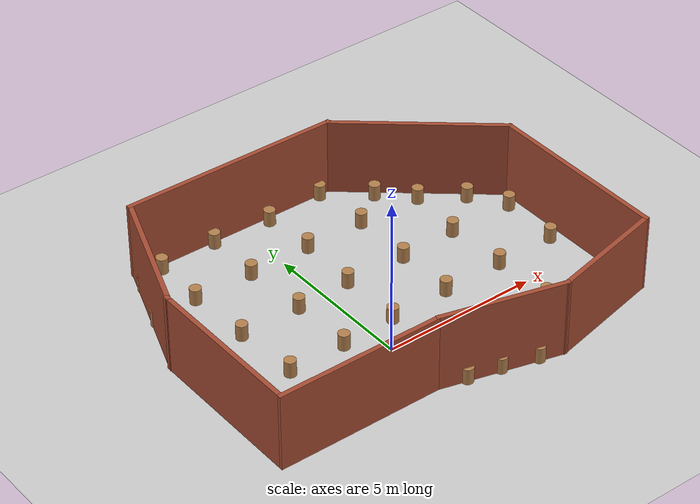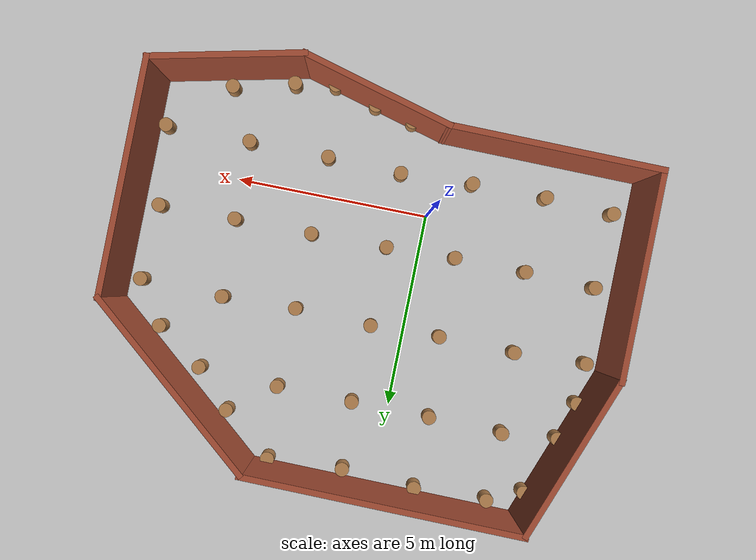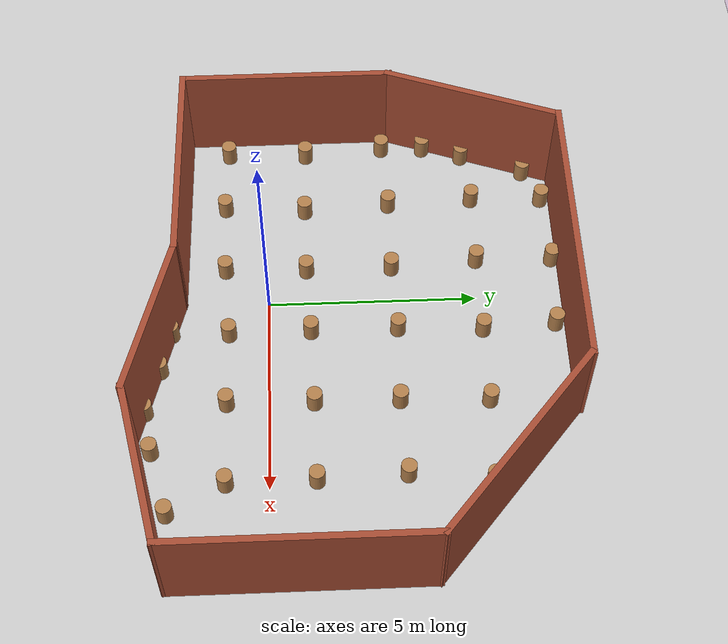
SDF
<sdf version="1.7">
 <world name="default">
  <light name="sun" type="directional">
   <pose>0 0 10 0 -0 0</pose>
   <diffuse>0.8 0.8 0.8 1</diffuse>
   <specular>0.2 0.2 0.2 1</specular>
   <attenuation>
    <range>1000</range>
    <constant>0.9</constant>
    <linear>0.01</linear>
    <quadratic>0.001</quadratic>
   </attenuation>
   <direction>-0.5 0.1 -0.9</direction>
   <spot><inner_angle>0</inner_angle><outer_angle>0</outer_angle><falloff>0</falloff></spot>
  </light>
  <model name="ground_plane">
   <static>1</static>
   <link name="link">
    <collision name="collision">
     <geometry><plane><normal>0 0 1</normal><size>100 100</size></plane></geometry>
     <surface>
      <contact><collide_bitmask>65535</collide_bitmask></contact>
      <friction><ode><mu>100</mu><mu2>50</mu2></ode></friction>
     </surface>
    </collision>
    <visual name="visual">
     <cast_shadows>0</cast_shadows>
     <geometry><plane><normal>0 0 1</normal><size>100 100</size></plane></geometry>
     <material>
      <script><uri>file://media/materials/scripts/gazebo.material</uri><name>Gazebo/Grey</name></script>
     </material>
    </visual>
   </link>
  </model>
  <gravity>0 0 -9.8</gravity>
  <magnetic_field>6e-06 2.3e-05 -4.2e-05</magnetic_field>
  <atmosphere type="adiabatic"/>
  <physics type="ode">
   <max_step_size>0.001</max_step_size>
   <real_time_factor>1</real_time_factor>
   <real_time_update_rate>1000</real_time_update_rate>
  </physics>
  <scene><ambient>0.4 0.4 0.4 1</ambient><background>0.7 0.7 0.7 1</background><shadows>1</shadows></scene>
  <spherical_coordinates>
   <surface_model>EARTH_WGS84</surface_model>
   <latitude_deg>0</latitude_deg>
   <longitude_deg>0</longitude_deg>
   <elevation>0</elevation>
   <heading_deg>0</heading_deg>
  </spherical_coordinates>
  <model name="arena">
   <pose>1.06818 2.30351 0 0 -0 0</pose>
   <link name="Wall_0">
    <collision name="Wall_0_Collision">
     <geometry><box><size>5.53276 0.15 2.5</size></box></geometry>
     <pose>0 0 1.25 0 -0 0</pose>
    </collision>
    <visual name="Wall_0_Visual">
     <pose>0 0 1.25 0 -0 0</pose>
     <geometry><box><size>5.53276 0.15 2.5</size></box></geometry>
     <material>
      <script><uri>file://media/materials/scripts/gazebo.material</uri><name>Gazebo/Bricks</name></script>
      <ambient>1 1 1 1</ambient>
     </material>
     <meta><layer>0</layer></meta>
    </visual>
    <pose>4.23522 3.04809 0 0 -0 -0.698052</pose>
   </link>
   <link name="Wall_1">
    <collision name="Wall_1_Collision">
     <geometry><box><size>6 0.15 2.5</size></box></geometry>
     <pose>0 0 1.25 0 -0 0</pose>
    </collision>
    <visual name="Wall_1_Visual">
     <pose>0 0 1.25 0 -0 0</pose>
     <geometry><box><size>6 0.15 2.5</size></box></geometry>
     <material>
      <script><uri>file://media/materials/scripts/gazebo.material</uri><name>Gazebo/Bricks</name></script>
      <ambient>1 1 1 1</ambient>
     </material>
     <meta><layer>0</layer></meta>
    </visual>
    <pose>6.29708 -1.60673 0 0 -0 -1.5708</pose>
   </link>
   <link name="Wall_2">
    <collision name="Wall_2_Collision">
     <geometry><box><size>3.91086 0.15 2.5</size></box></geometry>
     <pose>0 0 1.25 0 -0 0</pose>
    </collision>
    <visual name="Wall_2_Visual">
     <pose>0 0 1.25 0 -0 0</pose>
     <geometry><box><size>3.91086 0.15 2.5</size></box></geometry>
     <material>
      <script><uri>file://media/materials/scripts/gazebo.material</uri><name>Gazebo/Bricks</name></script>
      <ambient>1 1 1 1</ambient>
     </material>
     <meta><layer>0</layer></meta>
    </visual>
    <pose>4.46185 -4.94157 0 0 -0 -2.92188</pose>
   </link>
   <link name="Wall_3">
    <collision name="Wall_3_Collision">
     <geometry><box><size>4 0.15 2.5</size></box></geometry>
     <pose>0 0 1.25 0 -0 0</pose>
    </collision>
    <visual name="Wall_3_Visual">
     <pose>0 0 1.25 0 -0 0</pose>
     <geometry><box><size>4 0.15 2.5</size></box></geometry>
     <material>
      <script><uri>file://media/materials/scripts/gazebo.material</uri><name>Gazebo/Bricks</name></script>
      <ambient>1 1 1 1</ambient>
     </material>
     <meta><layer>0</layer></meta>
    </visual>
    <pose>0.76722 -4.85318 0 0 -0 2.87979</pose>
   </link>
   <link name="Wall_4">
    <collision name="Wall_4_Collision">
     <geometry><box><size>5.3647 0.15 2.5</size></box></geometry>
     <pose>0 0 1.25 0 -0 0</pose>
    </collision>
    <visual name="Wall_4_Visual">
     <pose>0 0 1.25 0 -0 0</pose>
     <geometry><box><size>5.3647 0.15 2.5</size></box></geometry>
     <material>
      <script><uri>file://media/materials/scripts/gazebo.material</uri><name>Gazebo/Bricks</name></script>
      <ambient>1 1 1 1</ambient>
     </material>
     <meta><layer>0</layer></meta>
    </visual>
    <pose>-3.69923 -4.33501 0 0 -0 3.13394</pose>
   </link>
   <link name="Wall_5">
    <collision name="Wall_5_Collision">
     <geometry><box><size>5.25 0.15 2.5</size></box></geometry>
     <pose>0 0 1.25 0 -0 0</pose>
    </collision>
    <visual name="Wall_5_Visual">
     <pose>0 0 1.25 0 -0 0</pose>
     <geometry><box><size>5.25 0.15 2.5</size></box></geometry>
     <material>
      <script><uri>file://media/materials/scripts/gazebo.material</uri><name>Gazebo/Bricks</name></script>
      <ambient>1 1 1 1</ambient>
     </material>
     <meta><layer>0</layer></meta>
    </visual>
    <pose>-6.30628 -1.72516 0 0 -0 1.5708</pose>
   </link>
   <link name="Wall_6">
    <collision name="Wall_6_Collision">
     <geometry><box><size>4.49397 0.15 2.5</size></box></geometry>
     <pose>0 0 1.25 0 -0 0</pose>
    </collision>
    <visual name="Wall_6_Visual">
     <pose>0 0 1.25 0 -0 0</pose>
     <geometry><box><size>4.49397 0.15 2.5</size></box></geometry>
     <material>
      <script><uri>file://media/materials/scripts/gazebo.material</uri><name>Gazebo/Bricks</name></script>
      <ambient>1 1 1 1</ambient>
     </material>
     <meta><layer>0</layer></meta>
    </visual>
    <pose>-5.54802 2.82027 0 0 -0 1.21418</pose>
   </link>
   <link name="Wall_7">
    <collision name="Wall_7_Collision">
     <geometry><box><size>7.11356 0.15 2.5</size></box></geometry>
     <pose>0 0 1.25 0 -0 0</pose>
    </collision>
    <visual name="Wall_7_Visual">
     <pose>0 0 1.25 0 -0 0</pose>
     <geometry><box><size>7.11356 0.15 2.5</size></box></geometry>
     <material>
      <script><uri>file://media/materials/scripts/gazebo.material</uri><name>Gazebo/Bricks</name></script>
      <ambient>1 1 1 1</ambient>
     </material>
     <meta><layer>0</layer></meta>
    </visual>
    <pose>-1.30819 4.85665 0 0 -0 -0.011157</pose>
   </link>
   <static>1</static>
  </model>
  <model name="wooden_block_clone_3">
   <link name="link_0">
    <inertial>
     <mass>145.751</mass>
     <inertia><ixx>13.3534</ixx><ixy>0</ixy><ixz>0</ixz><iyy>13.3534</iyy><iyz>0</iyz><izz>2.41499</izz></inertia>
    </inertial>
    <visual name="visual">
     <geometry><cylinder><radius>0.18204</radius><length>1</length></cylinder></geometry>
     <material>
      <lighting>1</lighting>
      <script><uri>file://media/materials/scripts/gazebo.material</uri><name>Gazebo/Wood</name></script>
      <shader type="pixel"><normal_map>__default__</normal_map></shader>
      <ambient>0.3 0.3 0.3 1</ambient>
      <diffuse>0.7 0.7 0.7 1</diffuse>
      <specular>0.01 0.01 0.01 1</specular>
      <emissive>0 0 0 1</emissive>
     </material>
    </visual>
    <collision name="collision">
     <geometry><cylinder><radius>0.18204</radius><length>1</length></cylinder></geometry>
     <surface>
      <friction>
       <ode><mu>1</mu><mu2>1</mu2><fdir1>0 0 0</fdir1><slip1>0</slip1><slip2>0</slip2></ode>
       <torsional>
        <coefficient>1</coefficient>
        <patch_radius>0</patch_radius>
        <surface_radius>0</surface_radius>
        <use_patch_radius>1</use_patch_radius>
        <ode><slip>0</slip></ode>
       </torsional>
      </friction>
      <bounce><restitution_coefficient>0</restitution_coefficient><threshold>1e+06</threshold></bounce>
      <contact>
       <collide_without_contact>0</collide_without_contact>
       <collide_without_contact_bitmask>1</collide_without_contact_bitmask>
       <collide_bitmask>1</collide_bitmask>
       <ode>
        <soft_cfm>0</soft_cfm>
        <soft_erp>0.2</soft_erp>
        <kp>1e+13</kp>
        <kd>1</kd>
        <max_vel>0.01</max_vel>
        <min_depth>0</min_depth>
       </ode>
       <bullet>
        <split_impulse>1</split_impulse>
        <split_impulse_penetration_threshold>-0.01</split_impulse_penetration_threshold>
        <soft_cfm>0</soft_cfm>
        <soft_erp>0.2</soft_erp>
        <kp>1e+13</kp>
        <kd>1</kd>
       </bullet>
      </contact>
     </surface>
    </collision>
   </link>
   <static>1</static>
   <pose>-0.943173 0.922976 0 0 -0 0</pose>
  </model>
  <model name="wooden_block_clone_3_clone">
   <link name="link_0">
    <inertial>
     <mass>145.751</mass>
     <inertia><ixx>13.3534</ixx><ixy>0</ixy><ixz>0</ixz><iyy>13.3534</iyy><iyz>0</iyz><izz>2.41499</izz></inertia>
    </inertial>
    <visual name="visual">
     <geometry><cylinder><radius>0.18204</radius><length>1</length></cylinder></geometry>
     <material>
      <lighting>1</lighting>
      <script><uri>file://media/materials/scripts/gazebo.material</uri><name>Gazebo/Wood</name></script>
      <shader type="pixel"><normal_map>__default__</normal_map></shader>
      <ambient>0.3 0.3 0.3 1</ambient>
      <diffuse>0.7 0.7 0.7 1</diffuse>
      <specular>0.01 0.01 0.01 1</specular>
      <emissive>0 0 0 1</emissive>
     </material>
    </visual>
    <collision name="collision">
     <geometry><cylinder><radius>0.18204</radius><length>1</length></cylinder></geometry>
     <surface>
      <friction>
       <ode><mu>1</mu><mu2>1</mu2><fdir1>0 0 0</fdir1><slip1>0</slip1><slip2>0</slip2></ode>
       <torsional>
        <coefficient>1</coefficient>
        <patch_radius>0</patch_radius>
        <surface_radius>0</surface_radius>
        <use_patch_radius>1</use_patch_radius>
        <ode><slip>0</slip></ode>
       </torsional>
      </friction>
      <bounce><restitution_coefficient>0</restitution_coefficient><threshold>1e+06</threshold></bounce>
      <contact>
       <collide_without_contact>0</collide_without_contact>
       <collide_without_contact_bitmask>1</collide_without_contact_bitmask>
       <collide_bitmask>1</collide_bitmask>
       <ode>
        <soft_cfm>0</soft_cfm>
        <soft_erp>0.2</soft_erp>
        <kp>1e+13</kp>
        <kd>1</kd>
        <max_vel>0.01</max_vel>
        <min_depth>0</min_depth>
       </ode>
       <bullet>
        <split_impulse>1</split_impulse>
        <split_impulse_penetration_threshold>-0.01</split_impulse_penetration_threshold>
        <soft_cfm>0</soft_cfm>
        <soft_erp>0.2</soft_erp>
        <kp>1e+13</kp>
        <kd>1</kd>
       </bullet>
      </contact>
     </surface>
    </collision>
   </link>
   <static>1</static>
   <pose>-2.80567 0.918212 0 0 -0 0</pose>
  </model>
  <model name="wooden_block_clone_3_clone_0">
   <link name="link_0">
    <inertial>
     <mass>145.751</mass>
     <inertia><ixx>13.3534</ixx><ixy>0</ixy><ixz>0</ixz><iyy>13.3534</iyy><iyz>0</iyz><izz>2.41499</izz></inertia>
    </inertial>
    <visual name="visual">
     <geometry><cylinder><radius>0.18204</radius><length>1</length></cylinder></geometry>
     <material>
      <lighting>1</lighting>
      <script><uri>file://media/materials/scripts/gazebo.material</uri><name>Gazebo/Wood</name></script>
      <shader type="pixel"><normal_map>__default__</normal_map></shader>
      <ambient>0.3 0.3 0.3 1</ambient>
      <diffuse>0.7 0.7 0.7 1</diffuse>
      <specular>0.01 0.01 0.01 1</specular>
      <emissive>0 0 0 1</emissive>
     </material>
    </visual>
    <collision name="collision">
     <geometry><cylinder><radius>0.18204</radius><length>1</length></cylinder></geometry>
     <surface>
      <friction>
       <ode><mu>1</mu><mu2>1</mu2><fdir1>0 0 0</fdir1><slip1>0</slip1><slip2>0</slip2></ode>
       <torsional>
        <coefficient>1</coefficient>
        <patch_radius>0</patch_radius>
        <surface_radius>0</surface_radius>
        <use_patch_radius>1</use_patch_radius>
        <ode><slip>0</slip></ode>
       </torsional>
      </friction>
      <bounce><restitution_coefficient>0</restitution_coefficient><threshold>1e+06</threshold></bounce>
      <contact>
       <collide_without_contact>0</collide_without_contact>
       <collide_without_contact_bitmask>1</collide_without_contact_bitmask>
       <collide_bitmask>1</collide_bitmask>
       <ode>
        <soft_cfm>0</soft_cfm>
        <soft_erp>0.2</soft_erp>
        <kp>1e+13</kp>
        <kd>1</kd>
        <max_vel>0.01</max_vel>
        <min_depth>0</min_depth>
       </ode>
       <bullet>
        <split_impulse>1</split_impulse>
        <split_impulse_penetration_threshold>-0.01</split_impulse_penetration_threshold>
        <soft_cfm>0</soft_cfm>
        <soft_erp>0.2</soft_erp>
        <kp>1e+13</kp>
        <kd>1</kd>
       </bullet>
      </contact>
     </surface>
    </collision>
   </link>
   <static>1</static>
   <pose>-4.64429 0.967972 0 0 -0 0</pose>
  </model>
  <model name="wooden_block_clone_3_clone_1">
   <link name="link_0">
    <inertial>
     <mass>145.751</mass>
     <inertia><ixx>13.3534</ixx><ixy>0</ixy><ixz>0</ixz><iyy>13.3534</iyy><iyz>0</iyz><izz>2.41499</izz></inertia>
    </inertial>
    <visual name="visual">
     <geometry><cylinder><radius>0.18204</radius><length>1</length></cylinder></geometry>
     <material>
      <lighting>1</lighting>
      <script><uri>file://media/materials/scripts/gazebo.material</uri><name>Gazebo/Wood</name></script>
      <shader type="pixel"><normal_map>__default__</normal_map></shader>
      <ambient>0.3 0.3 0.3 1</ambient>
      <diffuse>0.7 0.7 0.7 1</diffuse>
      <specular>0.01 0.01 0.01 1</specular>
      <emissive>0 0 0 1</emissive>
     </material>
    </visual>
    <collision name="collision">
     <geometry><cylinder><radius>0.18204</radius><length>1</length></cylinder></geometry>
     <surface>
      <friction>
       <ode><mu>1</mu><mu2>1</mu2><fdir1>0 0 0</fdir1><slip1>0</slip1><slip2>0</slip2></ode>
       <torsional>
        <coefficient>1</coefficient>
        <patch_radius>0</patch_radius>
        <surface_radius>0</surface_radius>
        <use_patch_radius>1</use_patch_radius>
        <ode><slip>0</slip></ode>
       </torsional>
      </friction>
      <bounce><restitution_coefficient>0</restitution_coefficient><threshold>1e+06</threshold></bounce>
      <contact>
       <collide_without_contact>0</collide_without_contact>
       <collide_without_contact_bitmask>1</collide_without_contact_bitmask>
       <collide_bitmask>1</collide_bitmask>
       <ode>
        <soft_cfm>0</soft_cfm>
        <soft_erp>0.2</soft_erp>
        <kp>1e+13</kp>
        <kd>1</kd>
        <max_vel>0.01</max_vel>
        <min_depth>0</min_depth>
       </ode>
       <bullet>
        <split_impulse>1</split_impulse>
        <split_impulse_penetration_threshold>-0.01</split_impulse_penetration_threshold>
        <soft_cfm>0</soft_cfm>
        <soft_erp>0.2</soft_erp>
        <kp>1e+13</kp>
        <kd>1</kd>
       </bullet>
      </contact>
     </surface>
    </collision>
   </link>
   <static>1</static>
   <pose>0.854333 1.00114 0 0 -0 0</pose>
  </model>
  <model name="wooden_block_clone_3_clone_2">
   <link name="link_0">
    <inertial>
     <mass>145.751</mass>
     <inertia><ixx>13.3534</ixx><ixy>0</ixy><ixz>0</ixz><iyy>13.3534</iyy><iyz>0</iyz><izz>2.41499</izz></inertia>
    </inertial>
    <visual name="visual">
     <geometry><cylinder><radius>0.18204</radius><length>1</length></cylinder></geometry>
     <material>
      <lighting>1</lighting>
      <script><uri>file://media/materials/scripts/gazebo.material</uri><name>Gazebo/Wood</name></script>
      <shader type="pixel"><normal_map>__default__</normal_map></shader>
      <ambient>0.3 0.3 0.3 1</ambient>
      <diffuse>0.7 0.7 0.7 1</diffuse>
      <specular>0.01 0.01 0.01 1</specular>
      <emissive>0 0 0 1</emissive>
     </material>
    </visual>
    <collision name="collision">
     <geometry><cylinder><radius>0.18204</radius><length>1</length></cylinder></geometry>
     <surface>
      <friction>
       <ode><mu>1</mu><mu2>1</mu2><fdir1>0 0 0</fdir1><slip1>0</slip1><slip2>0</slip2></ode>
       <torsional>
        <coefficient>1</coefficient>
        <patch_radius>0</patch_radius>
        <surface_radius>0</surface_radius>
        <use_patch_radius>1</use_patch_radius>
        <ode><slip>0</slip></ode>
       </torsional>
      </friction>
      <bounce><restitution_coefficient>0</restitution_coefficient><threshold>1e+06</threshold></bounce>
      <contact>
       <collide_without_contact>0</collide_without_contact>
       <collide_without_contact_bitmask>1</collide_without_contact_bitmask>
       <collide_bitmask>1</collide_bitmask>
       <ode>
        <soft_cfm>0</soft_cfm>
        <soft_erp>0.2</soft_erp>
        <kp>1e+13</kp>
        <kd>1</kd>
        <max_vel>0.01</max_vel>
        <min_depth>0</min_depth>
       </ode>
       <bullet>
        <split_impulse>1</split_impulse>
        <split_impulse_penetration_threshold>-0.01</split_impulse_penetration_threshold>
        <soft_cfm>0</soft_cfm>
        <soft_erp>0.2</soft_erp>
        <kp>1e+13</kp>
        <kd>1</kd>
       </bullet>
      </contact>
     </surface>
    </collision>
   </link>
   <static>1</static>
   <pose>0.865969 -0.949309 0 0 -0 0</pose>
  </model>
  <model name="wooden_block_clone_3_clone_3">
   <link name="link_0">
    <inertial>
     <mass>145.751</mass>
     <inertia><ixx>13.3534</ixx><ixy>0</ixy><ixz>0</ixz><iyy>13.3534</iyy><iyz>0</iyz><izz>2.41499</izz></inertia>
    </inertial>
    <visual name="visual">
     <geometry><cylinder><radius>0.18204</radius><length>1</length></cylinder></geometry>
     <material>
      <lighting>1</lighting>
      <script><uri>file://media/materials/scripts/gazebo.material</uri><name>Gazebo/Wood</name></script>
      <shader type="pixel"><normal_map>__default__</normal_map></shader>
      <ambient>0.3 0.3 0.3 1</ambient>
      <diffuse>0.7 0.7 0.7 1</diffuse>
      <specular>0.01 0.01 0.01 1</specular>
      <emissive>0 0 0 1</emissive>
     </material>
    </visual>
    <collision name="collision">
     <geometry><cylinder><radius>0.18204</radius><length>1</length></cylinder></geometry>
     <surface>
      <friction>
       <ode><mu>1</mu><mu2>1</mu2><fdir1>0 0 0</fdir1><slip1>0</slip1><slip2>0</slip2></ode>
       <torsional>
        <coefficient>1</coefficient>
        <patch_radius>0</patch_radius>
        <surface_radius>0</surface_radius>
        <use_patch_radius>1</use_patch_radius>
        <ode><slip>0</slip></ode>
       </torsional>
      </friction>
      <bounce><restitution_coefficient>0</restitution_coefficient><threshold>1e+06</threshold></bounce>
      <contact>
       <collide_without_contact>0</collide_without_contact>
       <collide_without_contact_bitmask>1</collide_without_contact_bitmask>
       <collide_bitmask>1</collide_bitmask>
       <ode>
        <soft_cfm>0</soft_cfm>
        <soft_erp>0.2</soft_erp>
        <kp>1e+13</kp>
        <kd>1</kd>
        <max_vel>0.01</max_vel>
        <min_depth>0</min_depth>
       </ode>
       <bullet>
        <split_impulse>1</split_impulse>
        <split_impulse_penetration_threshold>-0.01</split_impulse_penetration_threshold>
        <soft_cfm>0</soft_cfm>
        <soft_erp>0.2</soft_erp>
        <kp>1e+13</kp>
        <kd>1</kd>
       </bullet>
      </contact>
     </surface>
    </collision>
   </link>
   <static>1</static>
   <pose>2.79209 -0.988405 0 0 -0 0</pose>
  </model>
  <model name="wooden_block_clone_3_clone_4">
   <link name="link_0">
    <inertial>
     <mass>145.751</mass>
     <inertia><ixx>13.3534</ixx><ixy>0</ixy><ixz>0</ixz><iyy>13.3534</iyy><iyz>0</iyz><izz>2.41499</izz></inertia>
    </inertial>
    <visual name="visual">
     <geometry><cylinder><radius>0.18204</radius><length>1</length></cylinder></geometry>
     <material>
      <lighting>1</lighting>
      <script><uri>file://media/materials/scripts/gazebo.material</uri><name>Gazebo/Wood</name></script>
      <shader type="pixel"><normal_map>__default__</normal_map></shader>
      <ambient>0.3 0.3 0.3 1</ambient>
      <diffuse>0.7 0.7 0.7 1</diffuse>
      <specular>0.01 0.01 0.01 1</specular>
      <emissive>0 0 0 1</emissive>
     </material>
    </visual>
    <collision name="collision">
     <geometry><cylinder><radius>0.18204</radius><length>1</length></cylinder></geometry>
     <surface>
      <friction>
       <ode><mu>1</mu><mu2>1</mu2><fdir1>0 0 0</fdir1><slip1>0</slip1><slip2>0</slip2></ode>
       <torsional>
        <coefficient>1</coefficient>
        <patch_radius>0</patch_radius>
        <surface_radius>0</surface_radius>
        <use_patch_radius>1</use_patch_radius>
        <ode><slip>0</slip></ode>
       </torsional>
      </friction>
      <bounce><restitution_coefficient>0</restitution_coefficient><threshold>1e+06</threshold></bounce>
      <contact>
       <collide_without_contact>0</collide_without_contact>
       <collide_without_contact_bitmask>1</collide_without_contact_bitmask>
       <collide_bitmask>1</collide_bitmask>
       <ode>
        <soft_cfm>0</soft_cfm>
        <soft_erp>0.2</soft_erp>
        <kp>1e+13</kp>
        <kd>1</kd>
        <max_vel>0.01</max_vel>
        <min_depth>0</min_depth>
       </ode>
       <bullet>
        <split_impulse>1</split_impulse>
        <split_impulse_penetration_threshold>-0.01</split_impulse_penetration_threshold>
        <soft_cfm>0</soft_cfm>
        <soft_erp>0.2</soft_erp>
        <kp>1e+13</kp>
        <kd>1</kd>
       </bullet>
      </contact>
     </surface>
    </collision>
   </link>
   <static>1</static>
   <pose>2.83296 1.04178 0 0 -0 0</pose>
  </model>
  <model name="wooden_block_clone_3_clone_5">
   <link name="link_0">
    <inertial>
     <mass>145.751</mass>
     <inertia><ixx>13.3534</ixx><ixy>0</ixy><ixz>0</ixz><iyy>13.3534</iyy><iyz>0</iyz><izz>2.41499</izz></inertia>
    </inertial>
    <visual name="visual">
     <geometry><cylinder><radius>0.18204</radius><length>1</length></cylinder></geometry>
     <material>
      <lighting>1</lighting>
      <script><uri>file://media/materials/scripts/gazebo.material</uri><name>Gazebo/Wood</name></script>
      <shader type="pixel"><normal_map>__default__</normal_map></shader>
      <ambient>0.3 0.3 0.3 1</ambient>
      <diffuse>0.7 0.7 0.7 1</diffuse>
      <specular>0.01 0.01 0.01 1</specular>
      <emissive>0 0 0 1</emissive>
     </material>
    </visual>
    <collision name="collision">
     <geometry><cylinder><radius>0.18204</radius><length>1</length></cylinder></geometry>
     <surface>
      <friction>
       <ode><mu>1</mu><mu2>1</mu2><fdir1>0 0 0</fdir1><slip1>0</slip1><slip2>0</slip2></ode>
       <torsional>
        <coefficient>1</coefficient>
        <patch_radius>0</patch_radius>
        <surface_radius>0</surface_radius>
        <use_patch_radius>1</use_patch_radius>
        <ode><slip>0</slip></ode>
       </torsional>
      </friction>
      <bounce><restitution_coefficient>0</restitution_coefficient><threshold>1e+06</threshold></bounce>
      <contact>
       <collide_without_contact>0</collide_without_contact>
       <collide_without_contact_bitmask>1</collide_without_contact_bitmask>
       <collide_bitmask>1</collide_bitmask>
       <ode>
        <soft_cfm>0</soft_cfm>
        <soft_erp>0.2</soft_erp>
        <kp>1e+13</kp>
        <kd>1</kd>
        <max_vel>0.01</max_vel>
        <min_depth>0</min_depth>
       </ode>
       <bullet>
        <split_impulse>1</split_impulse>
        <split_impulse_penetration_threshold>-0.01</split_impulse_penetration_threshold>
        <soft_cfm>0</soft_cfm>
        <soft_erp>0.2</soft_erp>
        <kp>1e+13</kp>
        <kd>1</kd>
       </bullet>
      </contact>
     </surface>
    </collision>
   </link>
   <static>1</static>
   <pose>4.84954 1.05475 0 0 -0 0</pose>
  </model>
  <model name="wooden_block_clone_3_clone_6">
   <link name="link_0">
    <inertial>
     <mass>145.751</mass>
     <inertia><ixx>13.3534</ixx><ixy>0</ixy><ixz>0</ixz><iyy>13.3534</iyy><iyz>0</iyz><izz>2.41499</izz></inertia>
    </inertial>
    <visual name="visual">
     <geometry><cylinder><radius>0.18204</radius><length>1</length></cylinder></geometry>
     <material>
      <lighting>1</lighting>
      <script><uri>file://media/materials/scripts/gazebo.material</uri><name>Gazebo/Wood</name></script>
      <shader type="pixel"><normal_map>__default__</normal_map></shader>
      <ambient>0.3 0.3 0.3 1</ambient>
      <diffuse>0.7 0.7 0.7 1</diffuse>
      <specular>0.01 0.01 0.01 1</specular>
      <emissive>0 0 0 1</emissive>
     </material>
    </visual>
    <collision name="collision">
     <geometry><cylinder><radius>0.18204</radius><length>1</length></cylinder></geometry>
     <surface>
      <friction>
       <ode><mu>1</mu><mu2>1</mu2><fdir1>0 0 0</fdir1><slip1>0</slip1><slip2>0</slip2></ode>
       <torsional>
        <coefficient>1</coefficient>
        <patch_radius>0</patch_radius>
        <surface_radius>0</surface_radius>
        <use_patch_radius>1</use_patch_radius>
        <ode><slip>0</slip></ode>
       </torsional>
      </friction>
      <bounce><restitution_coefficient>0</restitution_coefficient><threshold>1e+06</threshold></bounce>
      <contact>
       <collide_without_contact>0</collide_without_contact>
       <collide_without_contact_bitmask>1</collide_without_contact_bitmask>
       <collide_bitmask>1</collide_bitmask>
       <ode>
        <soft_cfm>0</soft_cfm>
        <soft_erp>0.2</soft_erp>
        <kp>1e+13</kp>
        <kd>1</kd>
        <max_vel>0.01</max_vel>
        <min_depth>0</min_depth>
       </ode>
       <bullet>
        <split_impulse>1</split_impulse>
        <split_impulse_penetration_threshold>-0.01</split_impulse_penetration_threshold>
        <soft_cfm>0</soft_cfm>
        <soft_erp>0.2</soft_erp>
        <kp>1e+13</kp>
        <kd>1</kd>
       </bullet>
      </contact>
     </surface>
    </collision>
   </link>
   <static>1</static>
   <pose>4.86545 -0.986799 0 0 -0 0</pose>
  </model>
  <model name="wooden_block_clone_3_clone_7">
   <link name="link_0">
    <inertial>
     <mass>145.751</mass>
     <inertia><ixx>13.3534</ixx><ixy>0</ixy><ixz>0</ixz><iyy>13.3534</iyy><iyz>0</iyz><izz>2.41499</izz></inertia>
    </inertial>
    <visual name="visual">
     <geometry><cylinder><radius>0.18204</radius><length>1</length></cylinder></geometry>
     <material>
      <lighting>1</lighting>
      <script><uri>file://media/materials/scripts/gazebo.material</uri><name>Gazebo/Wood</name></script>
      <shader type="pixel"><normal_map>__default__</normal_map></shader>
      <ambient>0.3 0.3 0.3 1</ambient>
      <diffuse>0.7 0.7 0.7 1</diffuse>
      <specular>0.01 0.01 0.01 1</specular>
      <emissive>0 0 0 1</emissive>
     </material>
    </visual>
    <collision name="collision">
     <geometry><cylinder><radius>0.18204</radius><length>1</length></cylinder></geometry>
     <surface>
      <friction>
       <ode><mu>1</mu><mu2>1</mu2><fdir1>0 0 0</fdir1><slip1>0</slip1><slip2>0</slip2></ode>
       <torsional>
        <coefficient>1</coefficient>
        <patch_radius>0</patch_radius>
        <surface_radius>0</surface_radius>
        <use_patch_radius>1</use_patch_radius>
        <ode><slip>0</slip></ode>
       </torsional>
      </friction>
      <bounce><restitution_coefficient>0</restitution_coefficient><threshold>1e+06</threshold></bounce>
      <contact>
       <collide_without_contact>0</collide_without_contact>
       <collide_without_contact_bitmask>1</collide_without_contact_bitmask>
       <collide_bitmask>1</collide_bitmask>
       <ode>
        <soft_cfm>0</soft_cfm>
        <soft_erp>0.2</soft_erp>
        <kp>1e+13</kp>
        <kd>1</kd>
        <max_vel>0.01</max_vel>
        <min_depth>0</min_depth>
       </ode>
       <bullet>
        <split_impulse>1</split_impulse>
        <split_impulse_penetration_threshold>-0.01</split_impulse_penetration_threshold>
        <soft_cfm>0</soft_cfm>
        <soft_erp>0.2</soft_erp>
        <kp>1e+13</kp>
        <kd>1</kd>
       </bullet>
      </contact>
     </surface>
    </collision>
   </link>
   <static>1</static>
   <pose>6.83938 1.08948 0 0 -0 0</pose>
  </model>
  <model name="wooden_block_clone_3_clone_8">
   <link name="link_0">
    <inertial>
     <mass>145.751</mass>
     <inertia><ixx>13.3534</ixx><ixy>0</ixy><ixz>0</ixz><iyy>13.3534</iyy><iyz>0</iyz><izz>2.41499</izz></inertia>
    </inertial>
    <visual name="visual">
     <geometry><cylinder><radius>0.18204</radius><length>1</length></cylinder></geometry>
     <material>
      <lighting>1</lighting>
      <script><uri>file://media/materials/scripts/gazebo.material</uri><name>Gazebo/Wood</name></script>
      <shader type="pixel"><normal_map>__default__</normal_map></shader>
      <ambient>0.3 0.3 0.3 1</ambient>
      <diffuse>0.7 0.7 0.7 1</diffuse>
      <specular>0.01 0.01 0.01 1</specular>
      <emissive>0 0 0 1</emissive>
     </material>
    </visual>
    <collision name="collision">
     <geometry><cylinder><radius>0.18204</radius><length>1</length></cylinder></geometry>
     <surface>
      <friction>
       <ode><mu>1</mu><mu2>1</mu2><fdir1>0 0 0</fdir1><slip1>0</slip1><slip2>0</slip2></ode>
       <torsional>
        <coefficient>1</coefficient>
        <patch_radius>0</patch_radius>
        <surface_radius>0</surface_radius>
        <use_patch_radius>1</use_patch_radius>
        <ode><slip>0</slip></ode>
       </torsional>
      </friction>
      <bounce><restitution_coefficient>0</restitution_coefficient><threshold>1e+06</threshold></bounce>
      <contact>
       <collide_without_contact>0</collide_without_contact>
       <collide_without_contact_bitmask>1</collide_without_contact_bitmask>
       <collide_bitmask>1</collide_bitmask>
       <ode>
        <soft_cfm>0</soft_cfm>
        <soft_erp>0.2</soft_erp>
        <kp>1e+13</kp>
        <kd>1</kd>
        <max_vel>0.01</max_vel>
        <min_depth>0</min_depth>
       </ode>
       <bullet>
        <split_impulse>1</split_impulse>
        <split_impulse_penetration_threshold>-0.01</split_impulse_penetration_threshold>
        <soft_cfm>0</soft_cfm>
        <soft_erp>0.2</soft_erp>
        <kp>1e+13</kp>
        <kd>1</kd>
       </bullet>
      </contact>
     </surface>
    </collision>
   </link>
   <static>1</static>
   <pose>7.06622 -0.975193 0 0 -0 0</pose>
  </model>
  <model name="wooden_block_clone_3_clone_9">
   <link name="link_0">
    <inertial>
     <mass>145.751</mass>
     <inertia><ixx>13.3534</ixx><ixy>0</ixy><ixz>0</ixz><iyy>13.3534</iyy><iyz>0</iyz><izz>2.41499</izz></inertia>
    </inertial>
    <visual name="visual">
     <geometry><cylinder><radius>0.18204</radius><length>1</length></cylinder></geometry>
     <material>
      <lighting>1</lighting>
      <script><uri>file://media/materials/scripts/gazebo.material</uri><name>Gazebo/Wood</name></script>
      <shader type="pixel"><normal_map>__default__</normal_map></shader>
      <ambient>0.3 0.3 0.3 1</ambient>
      <diffuse>0.7 0.7 0.7 1</diffuse>
      <specular>0.01 0.01 0.01 1</specular>
      <emissive>0 0 0 1</emissive>
     </material>
    </visual>
    <collision name="collision">
     <geometry><cylinder><radius>0.18204</radius><length>1</length></cylinder></geometry>
     <surface>
      <friction>
       <ode><mu>1</mu><mu2>1</mu2><fdir1>0 0 0</fdir1><slip1>0</slip1><slip2>0</slip2></ode>
       <torsional>
        <coefficient>1</coefficient>
        <patch_radius>0</patch_radius>
        <surface_radius>0</surface_radius>
        <use_patch_radius>1</use_patch_radius>
        <ode><slip>0</slip></ode>
       </torsional>
      </friction>
      <bounce><restitution_coefficient>0</restitution_coefficient><threshold>1e+06</threshold></bounce>
      <contact>
       <collide_without_contact>0</collide_without_contact>
       <collide_without_contact_bitmask>1</collide_without_contact_bitmask>
       <collide_bitmask>1</collide_bitmask>
       <ode>
        <soft_cfm>0</soft_cfm>
        <soft_erp>0.2</soft_erp>
        <kp>1e+13</kp>
        <kd>1</kd>
        <max_vel>0.01</max_vel>
        <min_depth>0</min_depth>
       </ode>
       <bullet>
        <split_impulse>1</split_impulse>
        <split_impulse_penetration_threshold>-0.01</split_impulse_penetration_threshold>
        <soft_cfm>0</soft_cfm>
        <soft_erp>0.2</soft_erp>
        <kp>1e+13</kp>
        <kd>1</kd>
       </bullet>
      </contact>
     </surface>
    </collision>
   </link>
   <static>1</static>
   <pose>4.00547 -2.68421 0 0 -0 0</pose>
  </model>
  <model name="wooden_block_clone_3_clone_10">
   <link name="link_0">
    <inertial>
     <mass>145.751</mass>
     <inertia><ixx>13.3534</ixx><ixy>0</ixy><ixz>0</ixz><iyy>13.3534</iyy><iyz>0</iyz><izz>2.41499</izz></inertia>
    </inertial>
    <visual name="visual">
     <geometry><cylinder><radius>0.18204</radius><length>1</length></cylinder></geometry>
     <material>
      <lighting>1</lighting>
      <script><uri>file://media/materials/scripts/gazebo.material</uri><name>Gazebo/Wood</name></script>
      <shader type="pixel"><normal_map>__default__</normal_map></shader>
      <ambient>0.3 0.3 0.3 1</ambient>
      <diffuse>0.7 0.7 0.7 1</diffuse>
      <specular>0.01 0.01 0.01 1</specular>
      <emissive>0 0 0 1</emissive>
     </material>
    </visual>
    <collision name="collision">
     <geometry><cylinder><radius>0.18204</radius><length>1</length></cylinder></geometry>
     <surface>
      <friction>
       <ode><mu>1</mu><mu2>1</mu2><fdir1>0 0 0</fdir1><slip1>0</slip1><slip2>0</slip2></ode>
       <torsional>
        <coefficient>1</coefficient>
        <patch_radius>0</patch_radius>
        <surface_radius>0</surface_radius>
        <use_patch_radius>1</use_patch_radius>
        <ode><slip>0</slip></ode>
       </torsional>
      </friction>
      <bounce><restitution_coefficient>0</restitution_coefficient><threshold>1e+06</threshold></bounce>
      <contact>
       <collide_without_contact>0</collide_without_contact>
       <collide_without_contact_bitmask>1</collide_without_contact_bitmask>
       <collide_bitmask>1</collide_bitmask>
       <ode>
        <soft_cfm>0</soft_cfm>
        <soft_erp>0.2</soft_erp>
        <kp>1e+13</kp>
        <kd>1</kd>
        <max_vel>0.01</max_vel>
        <min_depth>0</min_depth>
       </ode>
       <bullet>
        <split_impulse>1</split_impulse>
        <split_impulse_penetration_threshold>-0.01</split_impulse_penetration_threshold>
        <soft_cfm>0</soft_cfm>
        <soft_erp>0.2</soft_erp>
        <kp>1e+13</kp>
        <kd>1</kd>
       </bullet>
      </contact>
     </surface>
    </collision>
   </link>
   <static>1</static>
   <pose>-1.01067 -1.04903 0 0 -0 0</pose>
  </model>
  <model name="wooden_block_clone_3_clone_11">
   <link name="link_0">
    <inertial>
     <mass>145.751</mass>
     <inertia><ixx>13.3534</ixx><ixy>0</ixy><ixz>0</ixz><iyy>13.3534</iyy><iyz>0</iyz><izz>2.41499</izz></inertia>
    </inertial>
    <visual name="visual">
     <geometry><cylinder><radius>0.18204</radius><length>1</length></cylinder></geometry>
     <material>
      <lighting>1</lighting>
      <script><uri>file://media/materials/scripts/gazebo.material</uri><name>Gazebo/Wood</name></script>
      <shader type="pixel"><normal_map>__default__</normal_map></shader>
      <ambient>0.3 0.3 0.3 1</ambient>
      <diffuse>0.7 0.7 0.7 1</diffuse>
      <specular>0.01 0.01 0.01 1</specular>
      <emissive>0 0 0 1</emissive>
     </material>
    </visual>
    <collision name="collision">
     <geometry><cylinder><radius>0.18204</radius><length>1</length></cylinder></geometry>
     <surface>
      <friction>
       <ode><mu>1</mu><mu2>1</mu2><fdir1>0 0 0</fdir1><slip1>0</slip1><slip2>0</slip2></ode>
       <torsional>
        <coefficient>1</coefficient>
        <patch_radius>0</patch_radius>
        <surface_radius>0</surface_radius>
        <use_patch_radius>1</use_patch_radius>
        <ode><slip>0</slip></ode>
       </torsional>
      </friction>
      <bounce><restitution_coefficient>0</restitution_coefficient><threshold>1e+06</threshold></bounce>
      <contact>
       <collide_without_contact>0</collide_without_contact>
       <collide_without_contact_bitmask>1</collide_without_contact_bitmask>
       <collide_bitmask>1</collide_bitmask>
       <ode>
        <soft_cfm>0</soft_cfm>
        <soft_erp>0.2</soft_erp>
        <kp>1e+13</kp>
        <kd>1</kd>
        <max_vel>0.01</max_vel>
        <min_depth>0</min_depth>
       </ode>
       <bullet>
        <split_impulse>1</split_impulse>
        <split_impulse_penetration_threshold>-0.01</split_impulse_penetration_threshold>
        <soft_cfm>0</soft_cfm>
        <soft_erp>0.2</soft_erp>
        <kp>1e+13</kp>
        <kd>1</kd>
       </bullet>
      </contact>
     </surface>
    </collision>
   </link>
   <static>1</static>
   <pose>-2.94864 -1.07437 0 0 -0 0</pose>
  </model>
  <model name="wooden_block_clone_3_clone_12">
   <link name="link_0">
    <inertial>
     <mass>145.751</mass>
     <inertia><ixx>13.3534</ixx><ixy>0</ixy><ixz>0</ixz><iyy>13.3534</iyy><iyz>0</iyz><izz>2.41499</izz></inertia>
    </inertial>
    <visual name="visual">
     <geometry><cylinder><radius>0.18204</radius><length>1</length></cylinder></geometry>
     <material>
      <lighting>1</lighting>
      <script><uri>file://media/materials/scripts/gazebo.material</uri><name>Gazebo/Wood</name></script>
      <shader type="pixel"><normal_map>__default__</normal_map></shader>
      <ambient>0.3 0.3 0.3 1</ambient>
      <diffuse>0.7 0.7 0.7 1</diffuse>
      <specular>0.01 0.01 0.01 1</specular>
      <emissive>0 0 0 1</emissive>
     </material>
    </visual>
    <collision name="collision">
     <geometry><cylinder><radius>0.18204</radius><length>1</length></cylinder></geometry>
     <surface>
      <friction>
       <ode><mu>1</mu><mu2>1</mu2><fdir1>0 0 0</fdir1><slip1>0</slip1><slip2>0</slip2></ode>
       <torsional>
        <coefficient>1</coefficient>
        <patch_radius>0</patch_radius>
        <surface_radius>0</surface_radius>
        <use_patch_radius>1</use_patch_radius>
        <ode><slip>0</slip></ode>
       </torsional>
      </friction>
      <bounce><restitution_coefficient>0</restitution_coefficient><threshold>1e+06</threshold></bounce>
      <contact>
       <collide_without_contact>0</collide_without_contact>
       <collide_without_contact_bitmask>1</collide_without_contact_bitmask>
       <collide_bitmask>1</collide_bitmask>
       <ode>
        <soft_cfm>0</soft_cfm>
        <soft_erp>0.2</soft_erp>
        <kp>1e+13</kp>
        <kd>1</kd>
        <max_vel>0.01</max_vel>
        <min_depth>0</min_depth>
       </ode>
       <bullet>
        <split_impulse>1</split_impulse>
        <split_impulse_penetration_threshold>-0.01</split_impulse_penetration_threshold>
        <soft_cfm>0</soft_cfm>
        <soft_erp>0.2</soft_erp>
        <kp>1e+13</kp>
        <kd>1</kd>
       </bullet>
      </contact>
     </surface>
    </collision>
   </link>
   <static>1</static>
   <pose>-4.72892 -1.00213 0 0 -0 0</pose>
  </model>
  <model name="wooden_block_clone_3_clone_13">
   <link name="link_0">
    <inertial>
     <mass>145.751</mass>
     <inertia><ixx>13.3534</ixx><ixy>0</ixy><ixz>0</ixz><iyy>13.3534</iyy><iyz>0</iyz><izz>2.41499</izz></inertia>
    </inertial>
    <visual name="visual">
     <geometry><cylinder><radius>0.18204</radius><length>1</length></cylinder></geometry>
     <material>
      <lighting>1</lighting>
      <script><uri>file://media/materials/scripts/gazebo.material</uri><name>Gazebo/Wood</name></script>
      <shader type="pixel"><normal_map>__default__</normal_map></shader>
      <ambient>0.3 0.3 0.3 1</ambient>
      <diffuse>0.7 0.7 0.7 1</diffuse>
      <specular>0.01 0.01 0.01 1</specular>
      <emissive>0 0 0 1</emissive>
     </material>
    </visual>
    <collision name="collision">
     <geometry><cylinder><radius>0.18204</radius><length>1</length></cylinder></geometry>
     <surface>
      <friction>
       <ode><mu>1</mu><mu2>1</mu2><fdir1>0 0 0</fdir1><slip1>0</slip1><slip2>0</slip2></ode>
       <torsional>
        <coefficient>1</coefficient>
        <patch_radius>0</patch_radius>
        <surface_radius>0</surface_radius>
        <use_patch_radius>1</use_patch_radius>
        <ode><slip>0</slip></ode>
       </torsional>
      </friction>
      <bounce><restitution_coefficient>0</restitution_coefficient><threshold>1e+06</threshold></bounce>
      <contact>
       <collide_without_contact>0</collide_without_contact>
       <collide_without_contact_bitmask>1</collide_without_contact_bitmask>
       <collide_bitmask>1</collide_bitmask>
       <ode>
        <soft_cfm>0</soft_cfm>
        <soft_erp>0.2</soft_erp>
        <kp>1e+13</kp>
        <kd>1</kd>
        <max_vel>0.01</max_vel>
        <min_depth>0</min_depth>
       </ode>
       <bullet>
        <split_impulse>1</split_impulse>
        <split_impulse_penetration_threshold>-0.01</split_impulse_penetration_threshold>
        <soft_cfm>0</soft_cfm>
        <soft_erp>0.2</soft_erp>
        <kp>1e+13</kp>
        <kd>1</kd>
       </bullet>
      </contact>
     </surface>
    </collision>
   </link>
   <static>1</static>
   <pose>-4.80726 2.93861 0 0 -0 0</pose>
  </model>
  <model name="wooden_block_clone_3_clone_14">
   <link name="link_0">
    <inertial>
     <mass>145.751</mass>
     <inertia><ixx>13.3534</ixx><ixy>0</ixy><ixz>0</ixz><iyy>13.3534</iyy><iyz>0</iyz><izz>2.41499</izz></inertia>
    </inertial>
    <visual name="visual">
     <geometry><cylinder><radius>0.18204</radius><length>1</length></cylinder></geometry>
     <material>
      <lighting>1</lighting>
      <script><uri>file://media/materials/scripts/gazebo.material</uri><name>Gazebo/Wood</name></script>
      <shader type="pixel"><normal_map>__default__</normal_map></shader>
      <ambient>0.3 0.3 0.3 1</ambient>
      <diffuse>0.7 0.7 0.7 1</diffuse>
      <specular>0.01 0.01 0.01 1</specular>
      <emissive>0 0 0 1</emissive>
     </material>
    </visual>
    <collision name="collision">
     <geometry><cylinder><radius>0.18204</radius><length>1</length></cylinder></geometry>
     <surface>
      <friction>
       <ode><mu>1</mu><mu2>1</mu2><fdir1>0 0 0</fdir1><slip1>0</slip1><slip2>0</slip2></ode>
       <torsional>
        <coefficient>1</coefficient>
        <patch_radius>0</patch_radius>
        <surface_radius>0</surface_radius>
        <use_patch_radius>1</use_patch_radius>
        <ode><slip>0</slip></ode>
       </torsional>
      </friction>
      <bounce><restitution_coefficient>0</restitution_coefficient><threshold>1e+06</threshold></bounce>
      <contact>
       <collide_without_contact>0</collide_without_contact>
       <collide_without_contact_bitmask>1</collide_without_contact_bitmask>
       <collide_bitmask>1</collide_bitmask>
       <ode>
        <soft_cfm>0</soft_cfm>
        <soft_erp>0.2</soft_erp>
        <kp>1e+13</kp>
        <kd>1</kd>
        <max_vel>0.01</max_vel>
        <min_depth>0</min_depth>
       </ode>
       <bullet>
        <split_impulse>1</split_impulse>
        <split_impulse_penetration_threshold>-0.01</split_impulse_penetration_threshold>
        <soft_cfm>0</soft_cfm>
        <soft_erp>0.2</soft_erp>
        <kp>1e+13</kp>
        <kd>1</kd>
       </bullet>
      </contact>
     </surface>
    </collision>
   </link>
   <static>1</static>
   <pose>-2.92813 3.02226 0 0 -0 0</pose>
  </model>
  <model name="wooden_block_clone_3_clone_15">
   <link name="link_0">
    <inertial>
     <mass>145.751</mass>
     <inertia><ixx>13.3534</ixx><ixy>0</ixy><ixz>0</ixz><iyy>13.3534</iyy><iyz>0</iyz><izz>2.41499</izz></inertia>
    </inertial>
    <visual name="visual">
     <geometry><cylinder><radius>0.18204</radius><length>1</length></cylinder></geometry>
     <material>
      <lighting>1</lighting>
      <script><uri>file://media/materials/scripts/gazebo.material</uri><name>Gazebo/Wood</name></script>
      <shader type="pixel"><normal_map>__default__</normal_map></shader>
      <ambient>0.3 0.3 0.3 1</ambient>
      <diffuse>0.7 0.7 0.7 1</diffuse>
      <specular>0.01 0.01 0.01 1</specular>
      <emissive>0 0 0 1</emissive>
     </material>
    </visual>
    <collision name="collision">
     <geometry><cylinder><radius>0.18204</radius><length>1</length></cylinder></geometry>
     <surface>
      <friction>
       <ode><mu>1</mu><mu2>1</mu2><fdir1>0 0 0</fdir1><slip1>0</slip1><slip2>0</slip2></ode>
       <torsional>
        <coefficient>1</coefficient>
        <patch_radius>0</patch_radius>
        <surface_radius>0</surface_radius>
        <use_patch_radius>1</use_patch_radius>
        <ode><slip>0</slip></ode>
       </torsional>
      </friction>
      <bounce><restitution_coefficient>0</restitution_coefficient><threshold>1e+06</threshold></bounce>
      <contact>
       <collide_without_contact>0</collide_without_contact>
       <collide_without_contact_bitmask>1</collide_without_contact_bitmask>
       <collide_bitmask>1</collide_bitmask>
       <ode>
        <soft_cfm>0</soft_cfm>
        <soft_erp>0.2</soft_erp>
        <kp>1e+13</kp>
        <kd>1</kd>
        <max_vel>0.01</max_vel>
        <min_depth>0</min_depth>
       </ode>
       <bullet>
        <split_impulse>1</split_impulse>
        <split_impulse_penetration_threshold>-0.01</split_impulse_penetration_threshold>
        <soft_cfm>0</soft_cfm>
        <soft_erp>0.2</soft_erp>
        <kp>1e+13</kp>
        <kd>1</kd>
       </bullet>
      </contact>
     </surface>
    </collision>
   </link>
   <static>1</static>
   <pose>-0.946331 3.00394 0 0 -0 0</pose>
  </model>
  <model name="wooden_block_clone_3_clone_16">
   <link name="link_0">
    <inertial>
     <mass>145.751</mass>
     <inertia><ixx>13.3534</ixx><ixy>0</ixy><ixz>0</ixz><iyy>13.3534</iyy><iyz>0</iyz><izz>2.41499</izz></inertia>
    </inertial>
    <visual name="visual">
     <geometry><cylinder><radius>0.18204</radius><length>1</length></cylinder></geometry>
     <material>
      <lighting>1</lighting>
      <script><uri>file://media/materials/scripts/gazebo.material</uri><name>Gazebo/Wood</name></script>
      <shader type="pixel"><normal_map>__default__</normal_map></shader>
      <ambient>0.3 0.3 0.3 1</ambient>
      <diffuse>0.7 0.7 0.7 1</diffuse>
      <specular>0.01 0.01 0.01 1</specular>
      <emissive>0 0 0 1</emissive>
     </material>
    </visual>
    <collision name="collision">
     <geometry><cylinder><radius>0.18204</radius><length>1</length></cylinder></geometry>
     <surface>
      <friction>
       <ode><mu>1</mu><mu2>1</mu2><fdir1>0 0 0</fdir1><slip1>0</slip1><slip2>0</slip2></ode>
       <torsional>
        <coefficient>1</coefficient>
        <patch_radius>0</patch_radius>
        <surface_radius>0</surface_radius>
        <use_patch_radius>1</use_patch_radius>
        <ode><slip>0</slip></ode>
       </torsional>
      </friction>
      <bounce><restitution_coefficient>0</restitution_coefficient><threshold>1e+06</threshold></bounce>
      <contact>
       <collide_without_contact>0</collide_without_contact>
       <collide_without_contact_bitmask>1</collide_without_contact_bitmask>
       <collide_bitmask>1</collide_bitmask>
       <ode>
        <soft_cfm>0</soft_cfm>
        <soft_erp>0.2</soft_erp>
        <kp>1e+13</kp>
        <kd>1</kd>
        <max_vel>0.01</max_vel>
        <min_depth>0</min_depth>
       </ode>
       <bullet>
        <split_impulse>1</split_impulse>
        <split_impulse_penetration_threshold>-0.01</split_impulse_penetration_threshold>
        <soft_cfm>0</soft_cfm>
        <soft_erp>0.2</soft_erp>
        <kp>1e+13</kp>
        <kd>1</kd>
       </bullet>
      </contact>
     </surface>
    </collision>
   </link>
   <static>1</static>
   <pose>0.857104 3.07098 0 0 -0 0</pose>
  </model>
  <model name="wooden_block_clone_3_clone_17">
   <link name="link_0">
    <inertial>
     <mass>145.751</mass>
     <inertia><ixx>13.3534</ixx><ixy>0</ixy><ixz>0</ixz><iyy>13.3534</iyy><iyz>0</iyz><izz>2.41499</izz></inertia>
    </inertial>
    <visual name="visual">
     <geometry><cylinder><radius>0.18204</radius><length>1</length></cylinder></geometry>
     <material>
      <lighting>1</lighting>
      <script><uri>file://media/materials/scripts/gazebo.material</uri><name>Gazebo/Wood</name></script>
      <shader type="pixel"><normal_map>__default__</normal_map></shader>
      <ambient>0.3 0.3 0.3 1</ambient>
      <diffuse>0.7 0.7 0.7 1</diffuse>
      <specular>0.01 0.01 0.01 1</specular>
      <emissive>0 0 0 1</emissive>
     </material>
    </visual>
    <collision name="collision">
     <geometry><cylinder><radius>0.18204</radius><length>1</length></cylinder></geometry>
     <surface>
      <friction>
       <ode><mu>1</mu><mu2>1</mu2><fdir1>0 0 0</fdir1><slip1>0</slip1><slip2>0</slip2></ode>
       <torsional>
        <coefficient>1</coefficient>
        <patch_radius>0</patch_radius>
        <surface_radius>0</surface_radius>
        <use_patch_radius>1</use_patch_radius>
        <ode><slip>0</slip></ode>
       </torsional>
      </friction>
      <bounce><restitution_coefficient>0</restitution_coefficient><threshold>1e+06</threshold></bounce>
      <contact>
       <collide_without_contact>0</collide_without_contact>
       <collide_without_contact_bitmask>1</collide_without_contact_bitmask>
       <collide_bitmask>1</collide_bitmask>
       <ode>
        <soft_cfm>0</soft_cfm>
        <soft_erp>0.2</soft_erp>
        <kp>1e+13</kp>
        <kd>1</kd>
        <max_vel>0.01</max_vel>
        <min_depth>0</min_depth>
       </ode>
       <bullet>
        <split_impulse>1</split_impulse>
        <split_impulse_penetration_threshold>-0.01</split_impulse_penetration_threshold>
        <soft_cfm>0</soft_cfm>
        <soft_erp>0.2</soft_erp>
        <kp>1e+13</kp>
        <kd>1</kd>
       </bullet>
      </contact>
     </surface>
    </collision>
   </link>
   <static>1</static>
   <pose>2.85236 3.01716 0 0 -0 0</pose>
  </model>
  <model name="wooden_block_clone_3_clone_18">
   <link name="link_0">
    <inertial>
     <mass>145.751</mass>
     <inertia><ixx>13.3534</ixx><ixy>0</ixy><ixz>0</ixz><iyy>13.3534</iyy><iyz>0</iyz><izz>2.41499</izz></inertia>
    </inertial>
    <visual name="visual">
     <geometry><cylinder><radius>0.18204</radius><length>1</length></cylinder></geometry>
     <material>
      <lighting>1</lighting>
      <script><uri>file://media/materials/scripts/gazebo.material</uri><name>Gazebo/Wood</name></script>
      <shader type="pixel"><normal_map>__default__</normal_map></shader>
      <ambient>0.3 0.3 0.3 1</ambient>
      <diffuse>0.7 0.7 0.7 1</diffuse>
      <specular>0.01 0.01 0.01 1</specular>
      <emissive>0 0 0 1</emissive>
     </material>
    </visual>
    <collision name="collision">
     <geometry><cylinder><radius>0.18204</radius><length>1</length></cylinder></geometry>
     <surface>
      <friction>
       <ode><mu>1</mu><mu2>1</mu2><fdir1>0 0 0</fdir1><slip1>0</slip1><slip2>0</slip2></ode>
       <torsional>
        <coefficient>1</coefficient>
        <patch_radius>0</patch_radius>
        <surface_radius>0</surface_radius>
        <use_patch_radius>1</use_patch_radius>
        <ode><slip>0</slip></ode>
       </torsional>
      </friction>
      <bounce><restitution_coefficient>0</restitution_coefficient><threshold>1e+06</threshold></bounce>
      <contact>
       <collide_without_contact>0</collide_without_contact>
       <collide_without_contact_bitmask>1</collide_without_contact_bitmask>
       <collide_bitmask>1</collide_bitmask>
       <ode>
        <soft_cfm>0</soft_cfm>
        <soft_erp>0.2</soft_erp>
        <kp>1e+13</kp>
        <kd>1</kd>
        <max_vel>0.01</max_vel>
        <min_depth>0</min_depth>
       </ode>
       <bullet>
        <split_impulse>1</split_impulse>
        <split_impulse_penetration_threshold>-0.01</split_impulse_penetration_threshold>
        <soft_cfm>0</soft_cfm>
        <soft_erp>0.2</soft_erp>
        <kp>1e+13</kp>
        <kd>1</kd>
       </bullet>
      </contact>
     </surface>
    </collision>
   </link>
   <static>1</static>
   <pose>4.7761 3.09299 0 0 -0 0</pose>
  </model>
  <model name="wooden_block_clone_3_clone_19">
   <link name="link_0">
    <inertial>
     <mass>145.751</mass>
     <inertia><ixx>13.3534</ixx><ixy>0</ixy><ixz>0</ixz><iyy>13.3534</iyy><iyz>0</iyz><izz>2.41499</izz></inertia>
    </inertial>
    <visual name="visual">
     <geometry><cylinder><radius>0.18204</radius><length>1</length></cylinder></geometry>
     <material>
      <lighting>1</lighting>
      <script><uri>file://media/materials/scripts/gazebo.material</uri><name>Gazebo/Wood</name></script>
      <shader type="pixel"><normal_map>__default__</normal_map></shader>
      <ambient>0.3 0.3 0.3 1</ambient>
      <diffuse>0.7 0.7 0.7 1</diffuse>
      <specular>0.01 0.01 0.01 1</specular>
      <emissive>0 0 0 1</emissive>
     </material>
    </visual>
    <collision name="collision">
     <geometry><cylinder><radius>0.18204</radius><length>1</length></cylinder></geometry>
     <surface>
      <friction>
       <ode><mu>1</mu><mu2>1</mu2><fdir1>0 0 0</fdir1><slip1>0</slip1><slip2>0</slip2></ode>
       <torsional>
        <coefficient>1</coefficient>
        <patch_radius>0</patch_radius>
        <surface_radius>0</surface_radius>
        <use_patch_radius>1</use_patch_radius>
        <ode><slip>0</slip></ode>
       </torsional>
      </friction>
      <bounce><restitution_coefficient>0</restitution_coefficient><threshold>1e+06</threshold></bounce>
      <contact>
       <collide_without_contact>0</collide_without_contact>
       <collide_without_contact_bitmask>1</collide_without_contact_bitmask>
       <collide_bitmask>1</collide_bitmask>
       <ode>
        <soft_cfm>0</soft_cfm>
        <soft_erp>0.2</soft_erp>
        <kp>1e+13</kp>
        <kd>1</kd>
        <max_vel>0.01</max_vel>
        <min_depth>0</min_depth>
       </ode>
       <bullet>
        <split_impulse>1</split_impulse>
        <split_impulse_penetration_threshold>-0.01</split_impulse_penetration_threshold>
        <soft_cfm>0</soft_cfm>
        <soft_erp>0.2</soft_erp>
        <kp>1e+13</kp>
        <kd>1</kd>
       </bullet>
      </contact>
     </surface>
    </collision>
   </link>
   <static>1</static>
   <pose>6.93099 3.04985 0 0 -0 0</pose>
  </model>
  <model name="wooden_block_clone_3_clone_20">
   <link name="link_0">
    <inertial>
     <mass>145.751</mass>
     <inertia><ixx>13.3534</ixx><ixy>0</ixy><ixz>0</ixz><iyy>13.3534</iyy><iyz>0</iyz><izz>2.41499</izz></inertia>
    </inertial>
    <visual name="visual">
     <geometry><cylinder><radius>0.18204</radius><length>1</length></cylinder></geometry>
     <material>
      <lighting>1</lighting>
      <script><uri>file://media/materials/scripts/gazebo.material</uri><name>Gazebo/Wood</name></script>
      <shader type="pixel"><normal_map>__default__</normal_map></shader>
      <ambient>0.3 0.3 0.3 1</ambient>
      <diffuse>0.7 0.7 0.7 1</diffuse>
      <specular>0.01 0.01 0.01 1</specular>
      <emissive>0 0 0 1</emissive>
     </material>
    </visual>
    <collision name="collision">
     <geometry><cylinder><radius>0.18204</radius><length>1</length></cylinder></geometry>
     <surface>
      <friction>
       <ode><mu>1</mu><mu2>1</mu2><fdir1>0 0 0</fdir1><slip1>0</slip1><slip2>0</slip2></ode>
       <torsional>
        <coefficient>1</coefficient>
        <patch_radius>0</patch_radius>
        <surface_radius>0</surface_radius>
        <use_patch_radius>1</use_patch_radius>
        <ode><slip>0</slip></ode>
       </torsional>
      </friction>
      <bounce><restitution_coefficient>0</restitution_coefficient><threshold>1e+06</threshold></bounce>
      <contact>
       <collide_without_contact>0</collide_without_contact>
       <collide_without_contact_bitmask>1</collide_without_contact_bitmask>
       <collide_bitmask>1</collide_bitmask>
       <ode>
        <soft_cfm>0</soft_cfm>
        <soft_erp>0.2</soft_erp>
        <kp>1e+13</kp>
        <kd>1</kd>
        <max_vel>0.01</max_vel>
        <min_depth>0</min_depth>
       </ode>
       <bullet>
        <split_impulse>1</split_impulse>
        <split_impulse_penetration_threshold>-0.01</split_impulse_penetration_threshold>
        <soft_cfm>0</soft_cfm>
        <soft_erp>0.2</soft_erp>
        <kp>1e+13</kp>
        <kd>1</kd>
       </bullet>
      </contact>
     </surface>
    </collision>
   </link>
   <static>1</static>
   <pose>5 5 0 0 -0 0</pose>
  </model>
  <model name="wooden_block_clone_3_clone_21">
   <link name="link_0">
    <inertial>
     <mass>145.751</mass>
     <inertia><ixx>13.3534</ixx><ixy>0</ixy><ixz>0</ixz><iyy>13.3534</iyy><iyz>0</iyz><izz>2.41499</izz></inertia>
    </inertial>
    <visual name="visual">
     <geometry><cylinder><radius>0.18204</radius><length>1</length></cylinder></geometry>
     <material>
      <lighting>1</lighting>
      <script><uri>file://media/materials/scripts/gazebo.material</uri><name>Gazebo/Wood</name></script>
      <shader type="pixel"><normal_map>__default__</normal_map></shader>
      <ambient>0.3 0.3 0.3 1</ambient>
      <diffuse>0.7 0.7 0.7 1</diffuse>
      <specular>0.01 0.01 0.01 1</specular>
      <emissive>0 0 0 1</emissive>
     </material>
    </visual>
    <collision name="collision">
     <geometry><cylinder><radius>0.18204</radius><length>1</length></cylinder></geometry>
     <surface>
      <friction>
       <ode><mu>1</mu><mu2>1</mu2><fdir1>0 0 0</fdir1><slip1>0</slip1><slip2>0</slip2></ode>
       <torsional>
        <coefficient>1</coefficient>
        <patch_radius>0</patch_radius>
        <surface_radius>0</surface_radius>
        <use_patch_radius>1</use_patch_radius>
        <ode><slip>0</slip></ode>
       </torsional>
      </friction>
      <bounce><restitution_coefficient>0</restitution_coefficient><threshold>1e+06</threshold></bounce>
      <contact>
       <collide_without_contact>0</collide_without_contact>
       <collide_without_contact_bitmask>1</collide_without_contact_bitmask>
       <collide_bitmask>1</collide_bitmask>
       <ode>
        <soft_cfm>0</soft_cfm>
        <soft_erp>0.2</soft_erp>
        <kp>1e+13</kp>
        <kd>1</kd>
        <max_vel>0.01</max_vel>
        <min_depth>0</min_depth>
       </ode>
       <bullet>
        <split_impulse>1</split_impulse>
        <split_impulse_penetration_threshold>-0.01</split_impulse_penetration_threshold>
        <soft_cfm>0</soft_cfm>
        <soft_erp>0.2</soft_erp>
        <kp>1e+13</kp>
        <kd>1</kd>
       </bullet>
      </contact>
     </surface>
    </collision>
   </link>
   <static>1</static>
   <pose>2.91853 5.08963 0 0 -0 0</pose>
  </model>
  <model name="wooden_block_clone_3_clone_22">
   <link name="link_0">
    <inertial>
     <mass>145.751</mass>
     <inertia><ixx>13.3534</ixx><ixy>0</ixy><ixz>0</ixz><iyy>13.3534</iyy><iyz>0</iyz><izz>2.41499</izz></inertia>
    </inertial>
    <visual name="visual">
     <geometry><cylinder><radius>0.18204</radius><length>1</length></cylinder></geometry>
     <material>
      <lighting>1</lighting>
      <script><uri>file://media/materials/scripts/gazebo.material</uri><name>Gazebo/Wood</name></script>
      <shader type="pixel"><normal_map>__default__</normal_map></shader>
      <ambient>0.3 0.3 0.3 1</ambient>
      <diffuse>0.7 0.7 0.7 1</diffuse>
      <specular>0.01 0.01 0.01 1</specular>
      <emissive>0 0 0 1</emissive>
     </material>
    </visual>
    <collision name="collision">
     <geometry><cylinder><radius>0.18204</radius><length>1</length></cylinder></geometry>
     <surface>
      <friction>
       <ode><mu>1</mu><mu2>1</mu2><fdir1>0 0 0</fdir1><slip1>0</slip1><slip2>0</slip2></ode>
       <torsional>
        <coefficient>1</coefficient>
        <patch_radius>0</patch_radius>
        <surface_radius>0</surface_radius>
        <use_patch_radius>1</use_patch_radius>
        <ode><slip>0</slip></ode>
       </torsional>
      </friction>
      <bounce><restitution_coefficient>0</restitution_coefficient><threshold>1e+06</threshold></bounce>
      <contact>
       <collide_without_contact>0</collide_without_contact>
       <collide_without_contact_bitmask>1</collide_without_contact_bitmask>
       <collide_bitmask>1</collide_bitmask>
       <ode>
        <soft_cfm>0</soft_cfm>
        <soft_erp>0.2</soft_erp>
        <kp>1e+13</kp>
        <kd>1</kd>
        <max_vel>0.01</max_vel>
        <min_depth>0</min_depth>
       </ode>
       <bullet>
        <split_impulse>1</split_impulse>
        <split_impulse_penetration_threshold>-0.01</split_impulse_penetration_threshold>
        <soft_cfm>0</soft_cfm>
        <soft_erp>0.2</soft_erp>
        <kp>1e+13</kp>
        <kd>1</kd>
       </bullet>
      </contact>
     </surface>
    </collision>
   </link>
   <static>1</static>
   <pose>0.951906 5.10145 0 0 -0 0</pose>
  </model>
  <model name="wooden_block_clone_3_clone_23">
   <link name="link_0">
    <inertial>
     <mass>145.751</mass>
     <inertia><ixx>13.3534</ixx><ixy>0</ixy><ixz>0</ixz><iyy>13.3534</iyy><iyz>0</iyz><izz>2.41499</izz></inertia>
    </inertial>
    <visual name="visual">
     <geometry><cylinder><radius>0.18204</radius><length>1</length></cylinder></geometry>
     <material>
      <lighting>1</lighting>
      <script><uri>file://media/materials/scripts/gazebo.material</uri><name>Gazebo/Wood</name></script>
      <shader type="pixel"><normal_map>__default__</normal_map></shader>
      <ambient>0.3 0.3 0.3 1</ambient>
      <diffuse>0.7 0.7 0.7 1</diffuse>
      <specular>0.01 0.01 0.01 1</specular>
      <emissive>0 0 0 1</emissive>
     </material>
    </visual>
    <collision name="collision">
     <geometry><cylinder><radius>0.18204</radius><length>1</length></cylinder></geometry>
     <surface>
      <friction>
       <ode><mu>1</mu><mu2>1</mu2><fdir1>0 0 0</fdir1><slip1>0</slip1><slip2>0</slip2></ode>
       <torsional>
        <coefficient>1</coefficient>
        <patch_radius>0</patch_radius>
        <surface_radius>0</surface_radius>
        <use_patch_radius>1</use_patch_radius>
        <ode><slip>0</slip></ode>
       </torsional>
      </friction>
      <bounce><restitution_coefficient>0</restitution_coefficient><threshold>1e+06</threshold></bounce>
      <contact>
       <collide_without_contact>0</collide_without_contact>
       <collide_without_contact_bitmask>1</collide_without_contact_bitmask>
       <collide_bitmask>1</collide_bitmask>
       <ode>
        <soft_cfm>0</soft_cfm>
        <soft_erp>0.2</soft_erp>
        <kp>1e+13</kp>
        <kd>1</kd>
        <max_vel>0.01</max_vel>
        <min_depth>0</min_depth>
       </ode>
       <bullet>
        <split_impulse>1</split_impulse>
        <split_impulse_penetration_threshold>-0.01</split_impulse_penetration_threshold>
        <soft_cfm>0</soft_cfm>
        <soft_erp>0.2</soft_erp>
        <kp>1e+13</kp>
        <kd>1</kd>
       </bullet>
      </contact>
     </surface>
    </collision>
   </link>
   <static>1</static>
   <pose>-1.09303 5.09757 0 0 -0 0</pose>
  </model>
  <model name="wooden_block_clone_3_clone_24">
   <link name="link_0">
    <inertial>
     <mass>145.751</mass>
     <inertia><ixx>13.3534</ixx><ixy>0</ixy><ixz>0</ixz><iyy>13.3534</iyy><iyz>0</iyz><izz>2.41499</izz></inertia>
    </inertial>
    <visual name="visual">
     <geometry><cylinder><radius>0.18204</radius><length>1</length></cylinder></geometry>
     <material>
      <lighting>1</lighting>
      <script><uri>file://media/materials/scripts/gazebo.material</uri><name>Gazebo/Wood</name></script>
      <shader type="pixel"><normal_map>__default__</normal_map></shader>
      <ambient>0.3 0.3 0.3 1</ambient>
      <diffuse>0.7 0.7 0.7 1</diffuse>
      <specular>0.01 0.01 0.01 1</specular>
      <emissive>0 0 0 1</emissive>
     </material>
    </visual>
    <collision name="collision">
     <geometry><cylinder><radius>0.18204</radius><length>1</length></cylinder></geometry>
     <surface>
      <friction>
       <ode><mu>1</mu><mu2>1</mu2><fdir1>0 0 0</fdir1><slip1>0</slip1><slip2>0</slip2></ode>
       <torsional>
        <coefficient>1</coefficient>
        <patch_radius>0</patch_radius>
        <surface_radius>0</surface_radius>
        <use_patch_radius>1</use_patch_radius>
        <ode><slip>0</slip></ode>
       </torsional>
      </friction>
      <bounce><restitution_coefficient>0</restitution_coefficient><threshold>1e+06</threshold></bounce>
      <contact>
       <collide_without_contact>0</collide_without_contact>
       <collide_without_contact_bitmask>1</collide_without_contact_bitmask>
       <collide_bitmask>1</collide_bitmask>
       <ode>
        <soft_cfm>0</soft_cfm>
        <soft_erp>0.2</soft_erp>
        <kp>1e+13</kp>
        <kd>1</kd>
        <max_vel>0.01</max_vel>
        <min_depth>0</min_depth>
       </ode>
       <bullet>
        <split_impulse>1</split_impulse>
        <split_impulse_penetration_threshold>-0.01</split_impulse_penetration_threshold>
        <soft_cfm>0</soft_cfm>
        <soft_erp>0.2</soft_erp>
        <kp>1e+13</kp>
        <kd>1</kd>
       </bullet>
      </contact>
     </surface>
    </collision>
   </link>
   <static>1</static>
   <pose>-3.02303 5.13273 0 0 -0 0</pose>
  </model>
  <model name="wooden_block_clone_3_clone_25">
   <link name="link_0">
    <inertial>
     <mass>145.751</mass>
     <inertia><ixx>13.3534</ixx><ixy>0</ixy><ixz>0</ixz><iyy>13.3534</iyy><iyz>0</iyz><izz>2.41499</izz></inertia>
    </inertial>
    <visual name="visual">
     <geometry><cylinder><radius>0.18204</radius><length>1</length></cylinder></geometry>
     <material>
      <lighting>1</lighting>
      <script><uri>file://media/materials/scripts/gazebo.material</uri><name>Gazebo/Wood</name></script>
      <shader type="pixel"><normal_map>__default__</normal_map></shader>
      <ambient>0.3 0.3 0.3 1</ambient>
      <diffuse>0.7 0.7 0.7 1</diffuse>
      <specular>0.01 0.01 0.01 1</specular>
      <emissive>0 0 0 1</emissive>
     </material>
    </visual>
    <collision name="collision">
     <geometry><cylinder><radius>0.18204</radius><length>1</length></cylinder></geometry>
     <surface>
      <friction>
       <ode><mu>1</mu><mu2>1</mu2><fdir1>0 0 0</fdir1><slip1>0</slip1><slip2>0</slip2></ode>
       <torsional>
        <coefficient>1</coefficient>
        <patch_radius>0</patch_radius>
        <surface_radius>0</surface_radius>
        <use_patch_radius>1</use_patch_radius>
        <ode><slip>0</slip></ode>
       </torsional>
      </friction>
      <bounce><restitution_coefficient>0</restitution_coefficient><threshold>1e+06</threshold></bounce>
      <contact>
       <collide_without_contact>0</collide_without_contact>
       <collide_without_contact_bitmask>1</collide_without_contact_bitmask>
       <collide_bitmask>1</collide_bitmask>
       <ode>
        <soft_cfm>0</soft_cfm>
        <soft_erp>0.2</soft_erp>
        <kp>1e+13</kp>
        <kd>1</kd>
        <max_vel>0.01</max_vel>
        <min_depth>0</min_depth>
       </ode>
       <bullet>
        <split_impulse>1</split_impulse>
        <split_impulse_penetration_threshold>-0.01</split_impulse_penetration_threshold>
        <soft_cfm>0</soft_cfm>
        <soft_erp>0.2</soft_erp>
        <kp>1e+13</kp>
        <kd>1</kd>
       </bullet>
      </contact>
     </surface>
    </collision>
   </link>
   <static>1</static>
   <pose>-2.96259 6.90565 0 0 -0 0</pose>
  </model>
  <model name="wooden_block_clone_3_clone_26">
   <link name="link_0">
    <inertial>
     <mass>145.751</mass>
     <inertia><ixx>13.3534</ixx><ixy>0</ixy><ixz>0</ixz><iyy>13.3534</iyy><iyz>0</iyz><izz>2.41499</izz></inertia>
    </inertial>
    <visual name="visual">
     <geometry><cylinder><radius>0.18204</radius><length>1</length></cylinder></geometry>
     <material>
      <lighting>1</lighting>
      <script><uri>file://media/materials/scripts/gazebo.material</uri><name>Gazebo/Wood</name></script>
      <shader type="pixel"><normal_map>__default__</normal_map></shader>
      <ambient>0.3 0.3 0.3 1</ambient>
      <diffuse>0.7 0.7 0.7 1</diffuse>
      <specular>0.01 0.01 0.01 1</specular>
      <emissive>0 0 0 1</emissive>
     </material>
    </visual>
    <collision name="collision">
     <geometry><cylinder><radius>0.18204</radius><length>1</length></cylinder></geometry>
     <surface>
      <friction>
       <ode><mu>1</mu><mu2>1</mu2><fdir1>0 0 0</fdir1><slip1>0</slip1><slip2>0</slip2></ode>
       <torsional>
        <coefficient>1</coefficient>
        <patch_radius>0</patch_radius>
        <surface_radius>0</surface_radius>
        <use_patch_radius>1</use_patch_radius>
        <ode><slip>0</slip></ode>
       </torsional>
      </friction>
      <bounce><restitution_coefficient>0</restitution_coefficient><threshold>1e+06</threshold></bounce>
      <contact>
       <collide_without_contact>0</collide_without_contact>
       <collide_without_contact_bitmask>1</collide_without_contact_bitmask>
       <collide_bitmask>1</collide_bitmask>
       <ode>
        <soft_cfm>0</soft_cfm>
        <soft_erp>0.2</soft_erp>
        <kp>1e+13</kp>
        <kd>1</kd>
        <max_vel>0.01</max_vel>
        <min_depth>0</min_depth>
       </ode>
       <bullet>
        <split_impulse>1</split_impulse>
        <split_impulse_penetration_threshold>-0.01</split_impulse_penetration_threshold>
        <soft_cfm>0</soft_cfm>
        <soft_erp>0.2</soft_erp>
        <kp>1e+13</kp>
        <kd>1</kd>
       </bullet>
      </contact>
     </surface>
    </collision>
   </link>
   <static>1</static>
   <pose>-1.06842 6.96489 0 0 -0 0</pose>
  </model>
  <model name="wooden_block_clone_3_clone_27">
   <link name="link_0">
    <inertial>
     <mass>145.751</mass>
     <inertia><ixx>13.3534</ixx><ixy>0</ixy><ixz>0</ixz><iyy>13.3534</iyy><iyz>0</iyz><izz>2.41499</izz></inertia>
    </inertial>
    <visual name="visual">
     <geometry><cylinder><radius>0.18204</radius><length>1</length></cylinder></geometry>
     <material>
      <lighting>1</lighting>
      <script><uri>file://media/materials/scripts/gazebo.material</uri><name>Gazebo/Wood</name></script>
      <shader type="pixel"><normal_map>__default__</normal_map></shader>
      <ambient>0.3 0.3 0.3 1</ambient>
      <diffuse>0.7 0.7 0.7 1</diffuse>
      <specular>0.01 0.01 0.01 1</specular>
      <emissive>0 0 0 1</emissive>
     </material>
    </visual>
    <collision name="collision">
     <geometry><cylinder><radius>0.18204</radius><length>1</length></cylinder></geometry>
     <surface>
      <friction>
       <ode><mu>1</mu><mu2>1</mu2><fdir1>0 0 0</fdir1><slip1>0</slip1><slip2>0</slip2></ode>
       <torsional>
        <coefficient>1</coefficient>
        <patch_radius>0</patch_radius>
        <surface_radius>0</surface_radius>
        <use_patch_radius>1</use_patch_radius>
        <ode><slip>0</slip></ode>
       </torsional>
      </friction>
      <bounce><restitution_coefficient>0</restitution_coefficient><threshold>1e+06</threshold></bounce>
      <contact>
       <collide_without_contact>0</collide_without_contact>
       <collide_without_contact_bitmask>1</collide_without_contact_bitmask>
       <collide_bitmask>1</collide_bitmask>
       <ode>
        <soft_cfm>0</soft_cfm>
        <soft_erp>0.2</soft_erp>
        <kp>1e+13</kp>
        <kd>1</kd>
        <max_vel>0.01</max_vel>
        <min_depth>0</min_depth>
       </ode>
       <bullet>
        <split_impulse>1</split_impulse>
        <split_impulse_penetration_threshold>-0.01</split_impulse_penetration_threshold>
        <soft_cfm>0</soft_cfm>
        <soft_erp>0.2</soft_erp>
        <kp>1e+13</kp>
        <kd>1</kd>
       </bullet>
      </contact>
     </surface>
    </collision>
   </link>
   <static>1</static>
   <pose>0.850256 6.85259 0 0 -0 0</pose>
  </model>
  <model name="wooden_block_clone_3_clone_28">
   <link name="link_0">
    <inertial>
     <mass>145.751</mass>
     <inertia><ixx>13.3534</ixx><ixy>0</ixy><ixz>0</ixz><iyy>13.3534</iyy><iyz>0</iyz><izz>2.41499</izz></inertia>
    </inertial>
    <visual name="visual">
     <geometry><cylinder><radius>0.18204</radius><length>1</length></cylinder></geometry>
     <material>
      <lighting>1</lighting>
      <script><uri>file://media/materials/scripts/gazebo.material</uri><name>Gazebo/Wood</name></script>
      <shader type="pixel"><normal_map>__default__</normal_map></shader>
      <ambient>0.3 0.3 0.3 1</ambient>
      <diffuse>0.7 0.7 0.7 1</diffuse>
      <specular>0.01 0.01 0.01 1</specular>
      <emissive>0 0 0 1</emissive>
     </material>
    </visual>
    <collision name="collision">
     <geometry><cylinder><radius>0.18204</radius><length>1</length></cylinder></geometry>
     <surface>
      <friction>
       <ode><mu>1</mu><mu2>1</mu2><fdir1>0 0 0</fdir1><slip1>0</slip1><slip2>0</slip2></ode>
       <torsional>
        <coefficient>1</coefficient>
        <patch_radius>0</patch_radius>
        <surface_radius>0</surface_radius>
        <use_patch_radius>1</use_patch_radius>
        <ode><slip>0</slip></ode>
       </torsional>
      </friction>
      <bounce><restitution_coefficient>0</restitution_coefficient><threshold>1e+06</threshold></bounce>
      <contact>
       <collide_without_contact>0</collide_without_contact>
       <collide_without_contact_bitmask>1</collide_without_contact_bitmask>
       <collide_bitmask>1</collide_bitmask>
       <ode>
        <soft_cfm>0</soft_cfm>
        <soft_erp>0.2</soft_erp>
        <kp>1e+13</kp>
        <kd>1</kd>
        <max_vel>0.01</max_vel>
        <min_depth>0</min_depth>
       </ode>
       <bullet>
        <split_impulse>1</split_impulse>
        <split_impulse_penetration_threshold>-0.01</split_impulse_penetration_threshold>
        <soft_cfm>0</soft_cfm>
        <soft_erp>0.2</soft_erp>
        <kp>1e+13</kp>
        <kd>1</kd>
       </bullet>
      </contact>
     </surface>
    </collision>
   </link>
   <static>1</static>
   <pose>2.80241 6.96834 0 0 -0 0</pose>
  </model>
  <model name="wooden_block_clone_3_clone_29">
   <link name="link_0">
    <inertial>
     <mass>145.751</mass>
     <inertia><ixx>13.3534</ixx><ixy>0</ixy><ixz>0</ixz><iyy>13.3534</iyy><iyz>0</iyz><izz>2.41499</izz></inertia>
    </inertial>
    <visual name="visual">
     <geometry><cylinder><radius>0.18204</radius><length>1</length></cylinder></geometry>
     <material>
      <lighting>1</lighting>
      <script><uri>file://media/materials/scripts/gazebo.material</uri><name>Gazebo/Wood</name></script>
      <shader type="pixel"><normal_map>__default__</normal_map></shader>
      <ambient>0.3 0.3 0.3 1</ambient>
      <diffuse>0.7 0.7 0.7 1</diffuse>
      <specular>0.01 0.01 0.01 1</specular>
      <emissive>0 0 0 1</emissive>
     </material>
    </visual>
    <collision name="collision">
     <geometry><cylinder><radius>0.18204</radius><length>1</length></cylinder></geometry>
     <surface>
      <friction>
       <ode><mu>1</mu><mu2>1</mu2><fdir1>0 0 0</fdir1><slip1>0</slip1><slip2>0</slip2></ode>
       <torsional>
        <coefficient>1</coefficient>
        <patch_radius>0</patch_radius>
        <surface_radius>0</surface_radius>
        <use_patch_radius>1</use_patch_radius>
        <ode><slip>0</slip></ode>
       </torsional>
      </friction>
      <bounce><restitution_coefficient>0</restitution_coefficient><threshold>1e+06</threshold></bounce>
      <contact>
       <collide_without_contact>0</collide_without_contact>
       <collide_without_contact_bitmask>1</collide_without_contact_bitmask>
       <collide_bitmask>1</collide_bitmask>
       <ode>
        <soft_cfm>0</soft_cfm>
        <soft_erp>0.2</soft_erp>
        <kp>1e+13</kp>
        <kd>1</kd>
        <max_vel>0.01</max_vel>
        <min_depth>0</min_depth>
       </ode>
       <bullet>
        <split_impulse>1</split_impulse>
        <split_impulse_penetration_threshold>-0.01</split_impulse_penetration_threshold>
        <soft_cfm>0</soft_cfm>
        <soft_erp>0.2</soft_erp>
        <kp>1e+13</kp>
        <kd>1</kd>
       </bullet>
      </contact>
     </surface>
    </collision>
   </link>
   <static>1</static>
   <pose>4.09134 5.94477 0 0 -0 0</pose>
  </model>
  <model name="wooden_block_clone_3_clone_30">
   <link name="link_0">
    <inertial>
     <mass>145.751</mass>
     <inertia><ixx>13.3534</ixx><ixy>0</ixy><ixz>0</ixz><iyy>13.3534</iyy><iyz>0</iyz><izz>2.41499</izz></inertia>
    </inertial>
    <visual name="visual">
     <geometry><cylinder><radius>0.18204</radius><length>1</length></cylinder></geometry>
     <material>
      <lighting>1</lighting>
      <script><uri>file://media/materials/scripts/gazebo.material</uri><name>Gazebo/Wood</name></script>
      <shader type="pixel"><normal_map>__default__</normal_map></shader>
      <ambient>0.3 0.3 0.3 1</ambient>
      <diffuse>0.7 0.7 0.7 1</diffuse>
      <specular>0.01 0.01 0.01 1</specular>
      <emissive>0 0 0 1</emissive>
     </material>
    </visual>
    <collision name="collision">
     <geometry><cylinder><radius>0.18204</radius><length>1</length></cylinder></geometry>
     <surface>
      <friction>
       <ode><mu>1</mu><mu2>1</mu2><fdir1>0 0 0</fdir1><slip1>0</slip1><slip2>0</slip2></ode>
       <torsional>
        <coefficient>1</coefficient>
        <patch_radius>0</patch_radius>
        <surface_radius>0</surface_radius>
        <use_patch_radius>1</use_patch_radius>
        <ode><slip>0</slip></ode>
       </torsional>
      </friction>
      <bounce><restitution_coefficient>0</restitution_coefficient><threshold>1e+06</threshold></bounce>
      <contact>
       <collide_without_contact>0</collide_without_contact>
       <collide_without_contact_bitmask>1</collide_without_contact_bitmask>
       <collide_bitmask>1</collide_bitmask>
       <ode>
        <soft_cfm>0</soft_cfm>
        <soft_erp>0.2</soft_erp>
        <kp>1e+13</kp>
        <kd>1</kd>
        <max_vel>0.01</max_vel>
        <min_depth>0</min_depth>
       </ode>
       <bullet>
        <split_impulse>1</split_impulse>
        <split_impulse_penetration_threshold>-0.01</split_impulse_penetration_threshold>
        <soft_cfm>0</soft_cfm>
        <soft_erp>0.2</soft_erp>
        <kp>1e+13</kp>
        <kd>1</kd>
       </bullet>
      </contact>
     </surface>
    </collision>
   </link>
   <static>1</static>
   <pose>6.21423 4.1498 0 0 -0 0</pose>
  </model>
  <model name="wooden_block_clone_3_clone_31">
   <link name="link_0">
    <inertial>
     <mass>145.751</mass>
     <inertia><ixx>13.3534</ixx><ixy>0</ixy><ixz>0</ixz><iyy>13.3534</iyy><iyz>0</iyz><izz>2.41499</izz></inertia>
    </inertial>
    <visual name="visual">
     <geometry><cylinder><radius>0.18204</radius><length>1</length></cylinder></geometry>
     <material>
      <lighting>1</lighting>
      <script><uri>file://media/materials/scripts/gazebo.material</uri><name>Gazebo/Wood</name></script>
      <shader type="pixel"><normal_map>__default__</normal_map></shader>
      <ambient>0.3 0.3 0.3 1</ambient>
      <diffuse>0.7 0.7 0.7 1</diffuse>
      <specular>0.01 0.01 0.01 1</specular>
      <emissive>0 0 0 1</emissive>
     </material>
    </visual>
    <collision name="collision">
     <geometry><cylinder><radius>0.18204</radius><length>1</length></cylinder></geometry>
     <surface>
      <friction>
       <ode><mu>1</mu><mu2>1</mu2><fdir1>0 0 0</fdir1><slip1>0</slip1><slip2>0</slip2></ode>
       <torsional>
        <coefficient>1</coefficient>
        <patch_radius>0</patch_radius>
        <surface_radius>0</surface_radius>
        <use_patch_radius>1</use_patch_radius>
        <ode><slip>0</slip></ode>
       </torsional>
      </friction>
      <bounce><restitution_coefficient>0</restitution_coefficient><threshold>1e+06</threshold></bounce>
      <contact>
       <collide_without_contact>0</collide_without_contact>
       <collide_without_contact_bitmask>1</collide_without_contact_bitmask>
       <collide_bitmask>1</collide_bitmask>
       <ode>
        <soft_cfm>0</soft_cfm>
        <soft_erp>0.2</soft_erp>
        <kp>1e+13</kp>
        <kd>1</kd>
        <max_vel>0.01</max_vel>
        <min_depth>0</min_depth>
       </ode>
       <bullet>
        <split_impulse>1</split_impulse>
        <split_impulse_penetration_threshold>-0.01</split_impulse_penetration_threshold>
        <soft_cfm>0</soft_cfm>
        <soft_erp>0.2</soft_erp>
        <kp>1e+13</kp>
        <kd>1</kd>
       </bullet>
      </contact>
     </surface>
    </collision>
   </link>
   <static>1</static>
   <pose>5.56674 -2.29209 0 0 -0 0</pose>
  </model>
  <model name="wooden_block_clone_3_clone_32">
   <link name="link_0">
    <inertial>
     <mass>145.751</mass>
     <inertia><ixx>13.3534</ixx><ixy>0</ixy><ixz>0</ixz><iyy>13.3534</iyy><iyz>0</iyz><izz>2.41499</izz></inertia>
    </inertial>
    <visual name="visual">
     <geometry><cylinder><radius>0.18204</radius><length>1</length></cylinder></geometry>
     <material>
      <lighting>1</lighting>
      <script><uri>file://media/materials/scripts/gazebo.material</uri><name>Gazebo/Wood</name></script>
      <shader type="pixel"><normal_map>__default__</normal_map></shader>
      <ambient>0.3 0.3 0.3 1</ambient>
      <diffuse>0.7 0.7 0.7 1</diffuse>
      <specular>0.01 0.01 0.01 1</specular>
      <emissive>0 0 0 1</emissive>
     </material>
    </visual>
    <collision name="collision">
     <geometry><cylinder><radius>0.18204</radius><length>1</length></cylinder></geometry>
     <surface>
      <friction>
       <ode><mu>1</mu><mu2>1</mu2><fdir1>0 0 0</fdir1><slip1>0</slip1><slip2>0</slip2></ode>
       <torsional>
        <coefficient>1</coefficient>
        <patch_radius>0</patch_radius>
        <surface_radius>0</surface_radius>
        <use_patch_radius>1</use_patch_radius>
        <ode><slip>0</slip></ode>
       </torsional>
      </friction>
      <bounce><restitution_coefficient>0</restitution_coefficient><threshold>1e+06</threshold></bounce>
      <contact>
       <collide_without_contact>0</collide_without_contact>
       <collide_without_contact_bitmask>1</collide_without_contact_bitmask>
       <collide_bitmask>1</collide_bitmask>
       <ode>
        <soft_cfm>0</soft_cfm>
        <soft_erp>0.2</soft_erp>
        <kp>1e+13</kp>
        <kd>1</kd>
        <max_vel>0.01</max_vel>
        <min_depth>0</min_depth>
       </ode>
       <bullet>
        <split_impulse>1</split_impulse>
        <split_impulse_penetration_threshold>-0.01</split_impulse_penetration_threshold>
        <soft_cfm>0</soft_cfm>
        <soft_erp>0.2</soft_erp>
        <kp>1e+13</kp>
        <kd>1</kd>
       </bullet>
      </contact>
     </surface>
    </collision>
   </link>
   <static>1</static>
   <pose>2.96521 -2.84906 0 0 -0 0</pose>
  </model>
  <model name="wooden_block_clone_3_clone_33">
   <link name="link_0">
    <inertial>
     <mass>145.751</mass>
     <inertia><ixx>13.3534</ixx><ixy>0</ixy><ixz>0</ixz><iyy>13.3534</iyy><iyz>0</iyz><izz>2.41499</izz></inertia>
    </inertial>
    <visual name="visual">
     <geometry><cylinder><radius>0.18204</radius><length>1</length></cylinder></geometry>
     <material>
      <lighting>1</lighting>
      <script><uri>file://media/materials/scripts/gazebo.material</uri><name>Gazebo/Wood</name></script>
      <shader type="pixel"><normal_map>__default__</normal_map></shader>
      <ambient>0.3 0.3 0.3 1</ambient>
      <diffuse>0.7 0.7 0.7 1</diffuse>
      <specular>0.01 0.01 0.01 1</specular>
      <emissive>0 0 0 1</emissive>
     </material>
    </visual>
    <collision name="collision">
     <geometry><cylinder><radius>0.18204</radius><length>1</length></cylinder></geometry>
     <surface>
      <friction>
       <ode><mu>1</mu><mu2>1</mu2><fdir1>0 0 0</fdir1><slip1>0</slip1><slip2>0</slip2></ode>
       <torsional>
        <coefficient>1</coefficient>
        <patch_radius>0</patch_radius>
        <surface_radius>0</surface_radius>
        <use_patch_radius>1</use_patch_radius>
        <ode><slip>0</slip></ode>
       </torsional>
      </friction>
      <bounce><restitution_coefficient>0</restitution_coefficient><threshold>1e+06</threshold></bounce>
      <contact>
       <collide_without_contact>0</collide_without_contact>
       <collide_without_contact_bitmask>1</collide_without_contact_bitmask>
       <collide_bitmask>1</collide_bitmask>
       <ode>
        <soft_cfm>0</soft_cfm>
        <soft_erp>0.2</soft_erp>
        <kp>1e+13</kp>
        <kd>1</kd>
        <max_vel>0.01</max_vel>
        <min_depth>0</min_depth>
       </ode>
       <bullet>
        <split_impulse>1</split_impulse>
        <split_impulse_penetration_threshold>-0.01</split_impulse_penetration_threshold>
        <soft_cfm>0</soft_cfm>
        <soft_erp>0.2</soft_erp>
        <kp>1e+13</kp>
        <kd>1</kd>
       </bullet>
      </contact>
     </surface>
    </collision>
   </link>
   <static>1</static>
   <pose>1.84641 -2.53994 0 0 -0 0</pose>
  </model>
  <model name="wooden_block_clone_3_clone_34">
   <link name="link_0">
    <inertial>
     <mass>145.751</mass>
     <inertia><ixx>13.3534</ixx><ixy>0</ixy><ixz>0</ixz><iyy>13.3534</iyy><iyz>0</iyz><izz>2.41499</izz></inertia>
    </inertial>
    <visual name="visual">
     <geometry><cylinder><radius>0.18204</radius><length>1</length></cylinder></geometry>
     <material>
      <lighting>1</lighting>
      <script><uri>file://media/materials/scripts/gazebo.material</uri><name>Gazebo/Wood</name></script>
      <shader type="pixel"><normal_map>__default__</normal_map></shader>
      <ambient>0.3 0.3 0.3 1</ambient>
      <diffuse>0.7 0.7 0.7 1</diffuse>
      <specular>0.01 0.01 0.01 1</specular>
      <emissive>0 0 0 1</emissive>
     </material>
    </visual>
    <collision name="collision">
     <geometry><cylinder><radius>0.18204</radius><length>1</length></cylinder></geometry>
     <surface>
      <friction>
       <ode><mu>1</mu><mu2>1</mu2><fdir1>0 0 0</fdir1><slip1>0</slip1><slip2>0</slip2></ode>
       <torsional>
        <coefficient>1</coefficient>
        <patch_radius>0</patch_radius>
        <surface_radius>0</surface_radius>
        <use_patch_radius>1</use_patch_radius>
        <ode><slip>0</slip></ode>
       </torsional>
      </friction>
      <bounce><restitution_coefficient>0</restitution_coefficient><threshold>1e+06</threshold></bounce>
      <contact>
       <collide_without_contact>0</collide_without_contact>
       <collide_without_contact_bitmask>1</collide_without_contact_bitmask>
       <collide_bitmask>1</collide_bitmask>
       <ode>
        <soft_cfm>0</soft_cfm>
        <soft_erp>0.2</soft_erp>
        <kp>1e+13</kp>
        <kd>1</kd>
        <max_vel>0.01</max_vel>
        <min_depth>0</min_depth>
       </ode>
       <bullet>
        <split_impulse>1</split_impulse>
        <split_impulse_penetration_threshold>-0.01</split_impulse_penetration_threshold>
        <soft_cfm>0</soft_cfm>
        <soft_erp>0.2</soft_erp>
        <kp>1e+13</kp>
        <kd>1</kd>
       </bullet>
      </contact>
     </surface>
    </collision>
   </link>
   <static>1</static>
   <pose>0.833721 -2.30812 0 0 -0 0</pose>
  </model>
  <model name="wooden_block_clone_3_clone_35">
   <link name="link_0">
    <inertial>
     <mass>145.751</mass>
     <inertia><ixx>13.3534</ixx><ixy>0</ixy><ixz>0</ixz><iyy>13.3534</iyy><iyz>0</iyz><izz>2.41499</izz></inertia>
    </inertial>
    <visual name="visual">
     <geometry><cylinder><radius>0.18204</radius><length>1</length></cylinder></geometry>
     <material>
      <lighting>1</lighting>
      <script><uri>file://media/materials/scripts/gazebo.material</uri><name>Gazebo/Wood</name></script>
      <shader type="pixel"><normal_map>__default__</normal_map></shader>
      <ambient>0.3 0.3 0.3 1</ambient>
      <diffuse>0.7 0.7 0.7 1</diffuse>
      <specular>0.01 0.01 0.01 1</specular>
      <emissive>0 0 0 1</emissive>
     </material>
    </visual>
    <collision name="collision">
     <geometry><cylinder><radius>0.18204</radius><length>1</length></cylinder></geometry>
     <surface>
      <friction>
       <ode><mu>1</mu><mu2>1</mu2><fdir1>0 0 0</fdir1><slip1>0</slip1><slip2>0</slip2></ode>
       <torsional>
        <coefficient>1</coefficient>
        <patch_radius>0</patch_radius>
        <surface_radius>0</surface_radius>
        <use_patch_radius>1</use_patch_radius>
        <ode><slip>0</slip></ode>
       </torsional>
      </friction>
      <bounce><restitution_coefficient>0</restitution_coefficient><threshold>1e+06</threshold></bounce>
      <contact>
       <collide_without_contact>0</collide_without_contact>
       <collide_without_contact_bitmask>1</collide_without_contact_bitmask>
       <collide_bitmask>1</collide_bitmask>
       <ode>
        <soft_cfm>0</soft_cfm>
        <soft_erp>0.2</soft_erp>
        <kp>1e+13</kp>
        <kd>1</kd>
        <max_vel>0.01</max_vel>
        <min_depth>0</min_depth>
       </ode>
       <bullet>
        <split_impulse>1</split_impulse>
        <split_impulse_penetration_threshold>-0.01</split_impulse_penetration_threshold>
        <soft_cfm>0</soft_cfm>
        <soft_erp>0.2</soft_erp>
        <kp>1e+13</kp>
        <kd>1</kd>
       </bullet>
      </contact>
     </surface>
    </collision>
   </link>
   <static>1</static>
   <pose>-3.86719 6.51831 0 0 -0 0</pose>
  </model>
  <model name="wooden_block_clone_3_clone_36">
   <link name="link_0">
    <inertial>
     <mass>145.751</mass>
     <inertia><ixx>13.3534</ixx><ixy>0</ixy><ixz>0</ixz><iyy>13.3534</iyy><iyz>0</iyz><izz>2.41499</izz></inertia>
    </inertial>
    <visual name="visual">
     <geometry><cylinder><radius>0.18204</radius><length>1</length></cylinder></geometry>
     <material>
      <lighting>1</lighting>
      <script><uri>file://media/materials/scripts/gazebo.material</uri><name>Gazebo/Wood</name></script>
      <shader type="pixel"><normal_map>__default__</normal_map></shader>
      <ambient>0.3 0.3 0.3 1</ambient>
      <diffuse>0.7 0.7 0.7 1</diffuse>
      <specular>0.01 0.01 0.01 1</specular>
      <emissive>0 0 0 1</emissive>
     </material>
    </visual>
    <collision name="collision">
     <geometry><cylinder><radius>0.18204</radius><length>1</length></cylinder></geometry>
     <surface>
      <friction>
       <ode><mu>1</mu><mu2>1</mu2><fdir1>0 0 0</fdir1><slip1>0</slip1><slip2>0</slip2></ode>
       <torsional>
        <coefficient>1</coefficient>
        <patch_radius>0</patch_radius>
        <surface_radius>0</surface_radius>
        <use_patch_radius>1</use_patch_radius>
        <ode><slip>0</slip></ode>
       </torsional>
      </friction>
      <bounce><restitution_coefficient>0</restitution_coefficient><threshold>1e+06</threshold></bounce>
      <contact>
       <collide_without_contact>0</collide_without_contact>
       <collide_without_contact_bitmask>1</collide_without_contact_bitmask>
       <collide_bitmask>1</collide_bitmask>
       <ode>
        <soft_cfm>0</soft_cfm>
        <soft_erp>0.2</soft_erp>
        <kp>1e+13</kp>
        <kd>1</kd>
        <max_vel>0.01</max_vel>
        <min_depth>0</min_depth>
       </ode>
       <bullet>
        <split_impulse>1</split_impulse>
        <split_impulse_penetration_threshold>-0.01</split_impulse_penetration_threshold>
        <soft_cfm>0</soft_cfm>
        <soft_erp>0.2</soft_erp>
        <kp>1e+13</kp>
        <kd>1</kd>
       </bullet>
      </contact>
     </surface>
    </collision>
   </link>
   <static>1</static>
   <pose>-4.45443 4.98441 0 0 -0 0</pose>
  </model>
  <model name="wooden_block_clone_3_clone_37">
   <link name="link_0">
    <inertial>
     <mass>145.751</mass>
     <inertia><ixx>13.3534</ixx><ixy>0</ixy><ixz>0</ixz><iyy>13.3534</iyy><iyz>0</iyz><izz>2.41499</izz></inertia>
    </inertial>
    <visual name="visual">
     <geometry><cylinder><radius>0.18204</radius><length>1</length></cylinder></geometry>
     <material>
      <lighting>1</lighting>
      <script><uri>file://media/materials/scripts/gazebo.material</uri><name>Gazebo/Wood</name></script>
      <shader type="pixel"><normal_map>__default__</normal_map></shader>
      <ambient>0.3 0.3 0.3 1</ambient>
      <diffuse>0.7 0.7 0.7 1</diffuse>
      <specular>0.01 0.01 0.01 1</specular>
      <emissive>0 0 0 1</emissive>
     </material>
    </visual>
    <collision name="collision">
     <geometry><cylinder><radius>0.18204</radius><length>1</length></cylinder></geometry>
     <surface>
      <friction>
       <ode><mu>1</mu><mu2>1</mu2><fdir1>0 0 0</fdir1><slip1>0</slip1><slip2>0</slip2></ode>
       <torsional>
        <coefficient>1</coefficient>
        <patch_radius>0</patch_radius>
        <surface_radius>0</surface_radius>
        <use_patch_radius>1</use_patch_radius>
        <ode><slip>0</slip></ode>
       </torsional>
      </friction>
      <bounce><restitution_coefficient>0</restitution_coefficient><threshold>1e+06</threshold></bounce>
      <contact>
       <collide_without_contact>0</collide_without_contact>
       <collide_without_contact_bitmask>1</collide_without_contact_bitmask>
       <collide_bitmask>1</collide_bitmask>
       <ode>
        <soft_cfm>0</soft_cfm>
        <soft_erp>0.2</soft_erp>
        <kp>1e+13</kp>
        <kd>1</kd>
        <max_vel>0.01</max_vel>
        <min_depth>0</min_depth>
       </ode>
       <bullet>
        <split_impulse>1</split_impulse>
        <split_impulse_penetration_threshold>-0.01</split_impulse_penetration_threshold>
        <soft_cfm>0</soft_cfm>
        <soft_erp>0.2</soft_erp>
        <kp>1e+13</kp>
        <kd>1</kd>
       </bullet>
      </contact>
     </surface>
    </collision>
   </link>
   <static>1</static>
   <pose>-4.77367 3.99587 0 0 -0 0</pose>
  </model>
 </world>
</sdf>
